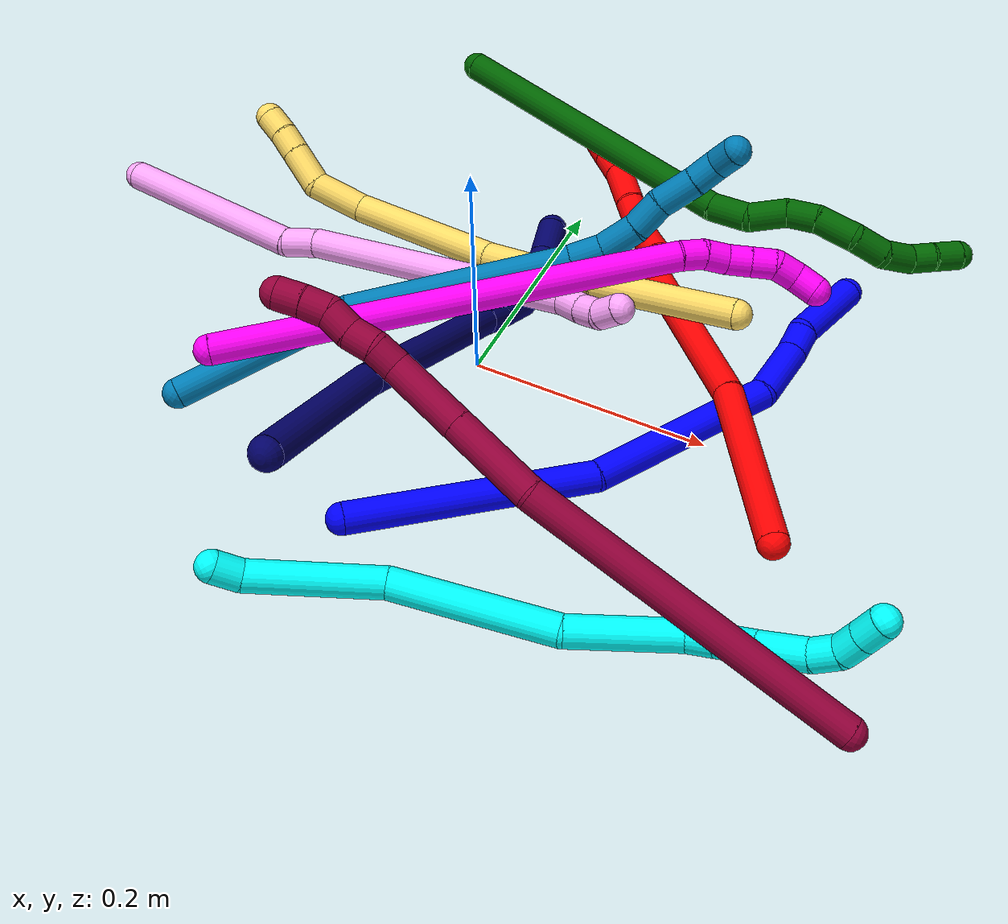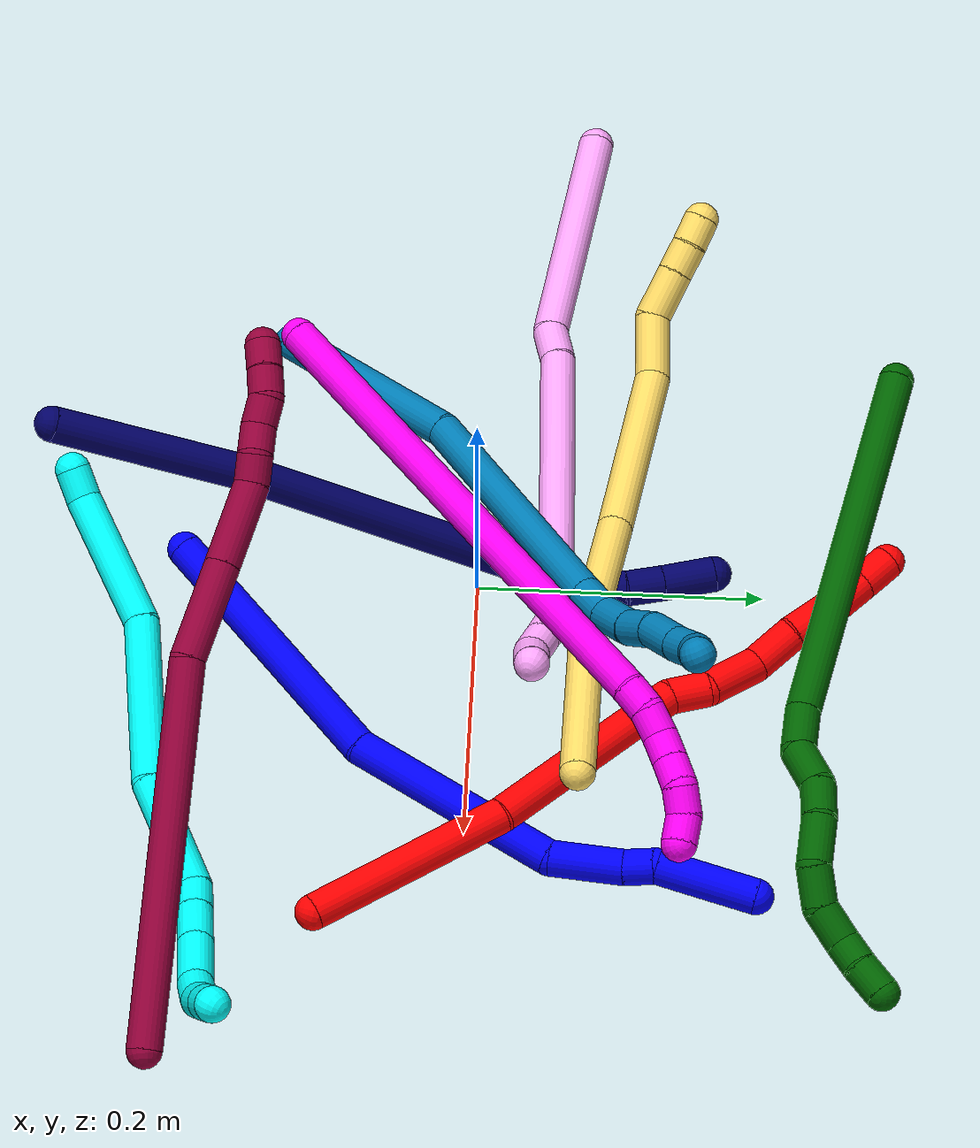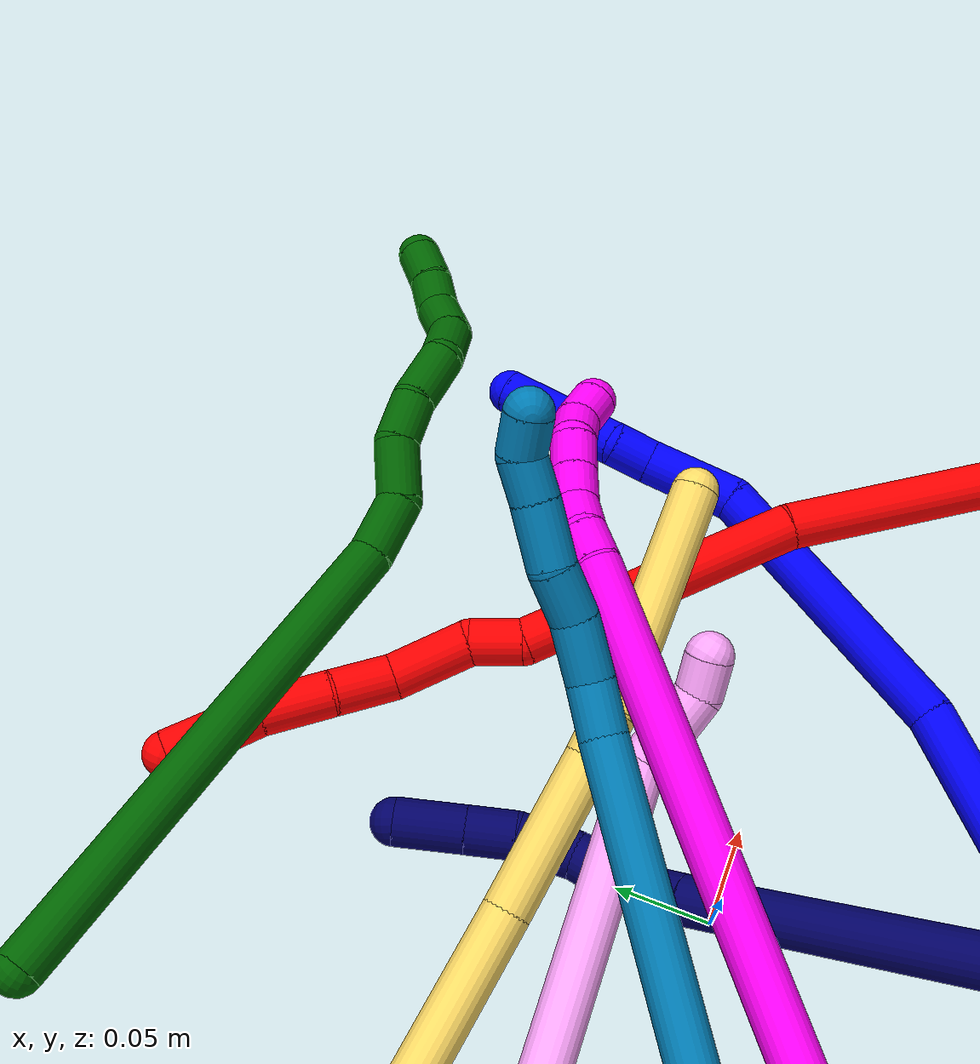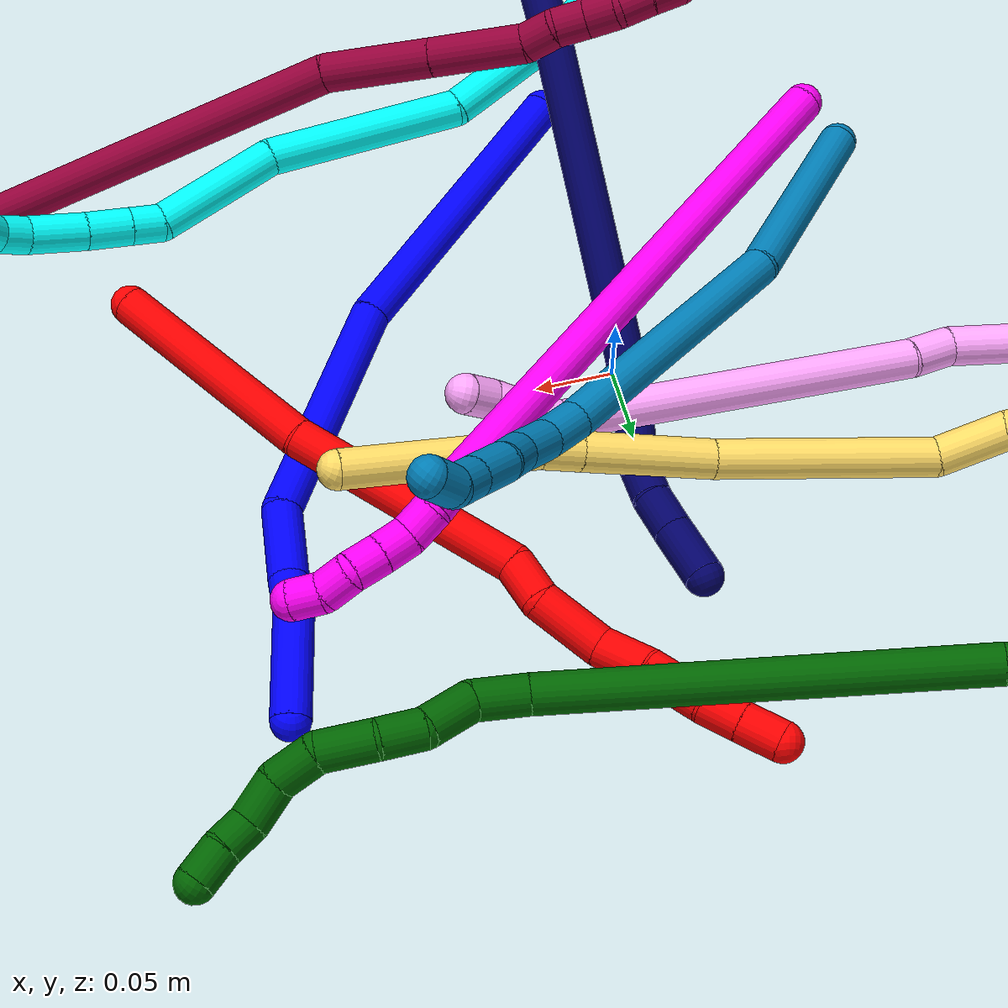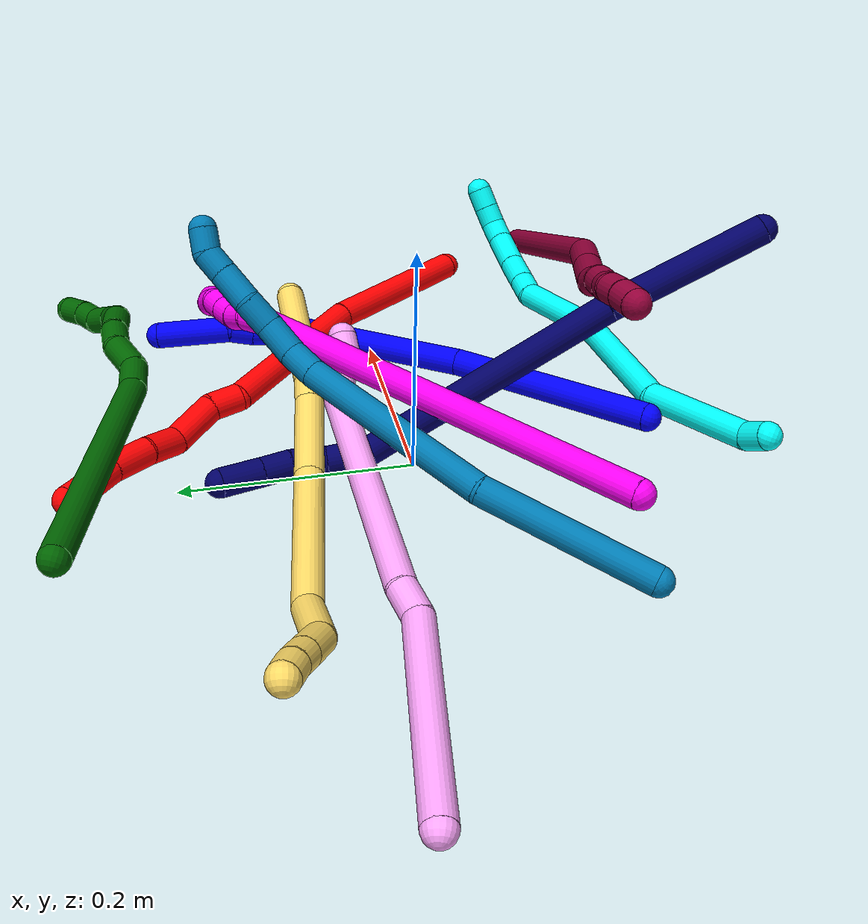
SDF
<sdf version="1.7">
 <world name="default">
  <plugin name="TubeGeneratorPlugin" filename="libtube_generator_plugin.so"/>
  <model name="photoneo_s_sensor">
   <static>1</static>
   <pose>0 0 2 1.57079 1.57079 3.14159</pose>
   <link name="link">
    <inertial><mass>0.1</mass></inertial>
    <sensor name="sensor" type="depth">
     <update_rate>30</update_rate>
     <camera>
      <horizontal_fov>1.22</horizontal_fov>
      <image><width>1920</width><height>1200</height><format>B8G8R8</format></image>
      <clip><near>0.1</near><far>2</far></clip>
      <depth_camera><output>points</output></depth_camera>
     </camera>
     <plugin name="camera_plugin" filename="libgazebo_ros_depth_camera.so">
      <baseline>0.2</baseline>
      <alwaysOn>1</alwaysOn>
      <updateRate>0.0</updateRate>
      <cameraName>camera_ir</cameraName>
      <imageTopicName>/camera/color/image_raw</imageTopicName>
      <cameraInfoTopicName>/camera/color/camera_info</cameraInfoTopicName>
      <depthImageTopicName>/camera/depth/image_raw</depthImageTopicName>
      <depthImageCameraInfoTopicName>/camera/depth/camera_info</depthImageCameraInfoTopicName>
      <pointCloudTopicName>/camera/depth/points</pointCloudTopicName>
      <frameName>fr_optical</frameName>
      <pointCloudCutoff>0.1</pointCloudCutoff>
      <pointCloudCutoffMax>2.0</pointCloudCutoffMax>
      <distortionK1>0</distortionK1>
      <distortionK2>0</distortionK2>
      <distortionK3>0</distortionK3>
      <distortionT1>0</distortionT1>
      <distortionT2>0</distortionT2>
      <CxPrime>0</CxPrime>
      <Cx>0</Cx>
      <Cy>0</Cy>
      <focalLength>0</focalLength>
      <hackBaseline>0</hackBaseline>
     </plugin>
    </sensor>
   </link>
  </model>
  <gravity>0 0 -9.8</gravity>
  <magnetic_field>6e-06 2.3e-05 -4.2e-05</magnetic_field>
  <atmosphere type="adiabatic"/>
  <physics name="default_physics" default="0" type="ode">
   <max_step_size>0.003</max_step_size>
   <real_time_factor>1</real_time_factor>
   <real_time_update_rate>1000</real_time_update_rate>
   <max_contacts>10000</max_contacts>
   <ode>
    <solver>
     <type>quick</type>
     <iters>100</iters>
     <sor>1.3</sor>
     <use_dynamic_moi_rescaling>0</use_dynamic_moi_rescaling>
    </solver>
    <constraints>
     <contact_max_correcting_vel>0</contact_max_correcting_vel>
     <contact_surface_layer>0.001</contact_surface_layer>
     <cfm>0</cfm>
     <erp>0.2</erp>
    </constraints>
   </ode>
  </physics>
  <scene><ambient>0.4 0.4 0.4 1</ambient><background>0.7 0.7 0.7 1</background><shadows>0</shadows></scene>
  <audio><device>default</device></audio>
  <spherical_coordinates>
   <surface_model>EARTH_WGS84</surface_model>
   <latitude_deg>0</latitude_deg>
   <longitude_deg>0</longitude_deg>
   <elevation>0</elevation>
   <heading_deg>0</heading_deg>
  </spherical_coordinates>
  <model name="bin">
   <static>1</static>
   <link name="bottom">
    <collision name="collision-bottom">
     <pose>0 0 -0.01 0 -0 0</pose>
     <geometry><box><size>0.8 0.6 0.02</size></box></geometry>
     <surface>
      <friction><ode><mu>100</mu><mu2>100</mu2></ode></friction>
      <contact><collide_bitmask>65535</collide_bitmask></contact>
     </surface>
    </collision>
   </link>
   <link name="west_wall">
    <collision name="collision-west_wall">
     <pose>-0.41 0 0.1 0 -0 0</pose>
     <geometry><box><size>0.02 0.6 0.2</size></box></geometry>
     <surface>
      <friction><ode><mu>100</mu><mu2>100</mu2></ode></friction>
      <contact><collide_bitmask>65535</collide_bitmask></contact>
     </surface>
    </collision>
   </link>
   <link name="east_wall">
    <collision name="collision-east_wall">
     <pose>0.41 0 0.1 0 -0 0</pose>
     <geometry><box><size>0.02 0.6 0.2</size></box></geometry>
     <surface>
      <friction><ode><mu>100</mu><mu2>100</mu2></ode></friction>
      <contact><collide_bitmask>65535</collide_bitmask></contact>
     </surface>
    </collision>
   </link>
   <link name="south_wall">
    <collision name="collision-south_wall">
     <pose>0 -0.31 0.1 0 -0 0</pose>
     <geometry><box><size>0.8 0.02 0.2</size></box></geometry>
     <surface>
      <friction><ode><mu>100</mu><mu2>100</mu2></ode></friction>
      <contact><collide_bitmask>65535</collide_bitmask></contact>
     </surface>
    </collision>
   </link>
   <link name="north_wall">
    <collision name="collision-north_wall">
     <pose>0 0.31 0.1 0 -0 0</pose>
     <geometry><box><size>0.8 0.02 0.2</size></box></geometry>
     <surface>
      <friction><ode><mu>100</mu><mu2>100</mu2></ode></friction>
      <contact><collide_bitmask>65535</collide_bitmask></contact>
     </surface>
    </collision>
   </link>
  </model>
  <model name="1">
   <static>0</static>
   <link name="1">
    <collision name="collision-cylinder-e_1_1_4">
     <pose>-0.056528 0.072189 -0.035755 -2.03067 -0.611869 0.941497</pose>
     <geometry><cylinder><radius>0.0125</radius><length>0.196825</length></cylinder></geometry>
     <surface>
      <friction><ode><mu>1.16</mu><mu2>1.16</mu2><slip1>0</slip1><slip2>0</slip2></ode></friction>
      <contact><ode><kp>1e+06</kp><kd>1</kd><max_vel>0</max_vel><min_depth>0.001</min_depth></ode></contact>
     </surface>
    </collision>
    <visual name="visual-cylinder-e_1_1_4">
     <pose>-0.056528 0.072189 -0.035755 -2.03067 -0.611869 0.941497</pose>
     <geometry><cylinder><radius>0.0125</radius><length>0.196825</length></cylinder></geometry>
     <material><ambient>0 0 1 1</ambient></material>
    </visual>
    <collision name="collision-cylinder-e_2_4_5">
     <pose>-0.175586 0.187292 -0.094243 -2.05796 -0.910455 1.36558</pose>
     <geometry><cylinder><radius>0.0125</radius><length>0.158346</length></cylinder></geometry>
     <surface>
      <friction><ode><mu>1.16</mu><mu2>1.16</mu2><slip1>0</slip1><slip2>0</slip2></ode></friction>
      <contact><ode><kp>1e+06</kp><kd>1</kd><max_vel>0</max_vel><min_depth>0.001</min_depth></ode></contact>
     </surface>
    </collision>
    <visual name="visual-cylinder-e_2_4_5">
     <pose>-0.175586 0.187292 -0.094243 -2.05796 -0.910455 1.36558</pose>
     <geometry><cylinder><radius>0.0125</radius><length>0.158346</length></cylinder></geometry>
     <material><ambient>0 0 1 1</ambient></material>
    </visual>
    <collision name="collision-cylinder-e_3_5_6">
     <pose>-0.262917 0.233619 -0.123517 -2.66053 -1.28167 2.50615</pose>
     <geometry><cylinder><radius>0.0125</radius><length>0.051752</length></cylinder></geometry>
     <surface>
      <friction><ode><mu>1.16</mu><mu2>1.16</mu2><slip1>0</slip1><slip2>0</slip2></ode></friction>
      <contact><ode><kp>1e+06</kp><kd>1</kd><max_vel>0</max_vel><min_depth>0.001</min_depth></ode></contact>
     </surface>
    </collision>
    <visual name="visual-cylinder-e_3_5_6">
     <pose>-0.262917 0.233619 -0.123517 -2.66053 -1.28167 2.50615</pose>
     <geometry><cylinder><radius>0.0125</radius><length>0.051752</length></cylinder></geometry>
     <material><ambient>0 0 1 1</ambient></material>
    </visual>
    <collision name="collision-cylinder-e_4_6_7">
     <pose>-0.298862 0.238176 -0.130409 -1.86924 -1.46391 1.76544</pose>
     <geometry><cylinder><radius>0.0125</radius><length>0.022414</length></cylinder></geometry>
     <surface>
      <friction><ode><mu>1.16</mu><mu2>1.16</mu2><slip1>0</slip1><slip2>0</slip2></ode></friction>
      <contact><ode><kp>1e+06</kp><kd>1</kd><max_vel>0</max_vel><min_depth>0.001</min_depth></ode></contact>
     </surface>
    </collision>
    <visual name="visual-cylinder-e_4_6_7">
     <pose>-0.298862 0.238176 -0.130409 -1.86924 -1.46391 1.76544</pose>
     <geometry><cylinder><radius>0.0125</radius><length>0.022414</length></cylinder></geometry>
     <material><ambient>0 0 1 1</ambient></material>
    </visual>
    <collision name="collision-cylinder-e_5_7_2">
     <pose>-0.341504 0.247161 -0.14471 -2.62943 -1.10072 2.33495</pose>
     <geometry><cylinder><radius>0.0125</radius><length>0.070663</length></cylinder></geometry>
     <surface>
      <friction><ode><mu>1.16</mu><mu2>1.16</mu2><slip1>0</slip1><slip2>0</slip2></ode></friction>
      <contact><ode><kp>1e+06</kp><kd>1</kd><max_vel>0</max_vel><min_depth>0.001</min_depth></ode></contact>
     </surface>
    </collision>
    <visual name="visual-cylinder-e_5_7_2">
     <pose>-0.341504 0.247161 -0.14471 -2.62943 -1.10072 2.33495</pose>
     <geometry><cylinder><radius>0.0125</radius><length>0.070663</length></cylinder></geometry>
     <material><ambient>0 0 1 1</ambient></material>
    </visual>
    <collision name="collision-sphere-2">
     <pose>-0.373003 0.255004 -0.158661 0 -0 0</pose>
     <geometry><sphere><radius>0.0125</radius></sphere></geometry>
     <surface>
      <friction><ode><mu>1.16</mu><mu2>1.16</mu2><slip1>0</slip1><slip2>0</slip2></ode></friction>
      <contact><ode><kp>1e+06</kp><kd>1</kd><max_vel>0</max_vel><min_depth>0.001</min_depth></ode></contact>
     </surface>
    </collision>
    <visual name="visual-sphere-2">
     <pose>-0.373003 0.255004 -0.158661 0 -0 0</pose>
     <geometry><sphere><radius>0.0125</radius></sphere></geometry>
     <material><ambient>0 0 1 1</ambient></material>
    </visual>
    <collision name="collision-sphere-7">
     <pose>-0.310005 0.239319 -0.13076 0 -0 0</pose>
     <geometry><sphere><radius>0.0125</radius></sphere></geometry>
     <surface>
      <friction><ode><mu>1.16</mu><mu2>1.16</mu2><slip1>0</slip1><slip2>0</slip2></ode></friction>
      <contact><ode><kp>1e+06</kp><kd>1</kd><max_vel>0</max_vel><min_depth>0.001</min_depth></ode></contact>
     </surface>
    </collision>
    <visual name="visual-sphere-7">
     <pose>-0.310005 0.239319 -0.13076 0 -0 0</pose>
     <geometry><sphere><radius>0.0125</radius></sphere></geometry>
     <material><ambient>0 0 1 1</ambient></material>
    </visual>
    <collision name="collision-sphere-6">
     <pose>-0.287719 0.237033 -0.130057 0 -0 0</pose>
     <geometry><sphere><radius>0.0125</radius></sphere></geometry>
     <surface>
      <friction><ode><mu>1.16</mu><mu2>1.16</mu2><slip1>0</slip1><slip2>0</slip2></ode></friction>
      <contact><ode><kp>1e+06</kp><kd>1</kd><max_vel>0</max_vel><min_depth>0.001</min_depth></ode></contact>
     </surface>
    </collision>
    <visual name="visual-sphere-6">
     <pose>-0.287719 0.237033 -0.130057 0 -0 0</pose>
     <geometry><sphere><radius>0.0125</radius></sphere></geometry>
     <material><ambient>0 0 1 1</ambient></material>
    </visual>
    <collision name="collision-sphere-5">
     <pose>-0.238115 0.230206 -0.116977 0 -0 0</pose>
     <geometry><sphere><radius>0.0125</radius></sphere></geometry>
     <surface>
      <friction><ode><mu>1.16</mu><mu2>1.16</mu2><slip1>0</slip1><slip2>0</slip2></ode></friction>
      <contact><ode><kp>1e+06</kp><kd>1</kd><max_vel>0</max_vel><min_depth>0.001</min_depth></ode></contact>
     </surface>
    </collision>
    <visual name="visual-sphere-5">
     <pose>-0.238115 0.230206 -0.116977 0 -0 0</pose>
     <geometry><sphere><radius>0.0125</radius></sphere></geometry>
     <material><ambient>0 0 1 1</ambient></material>
    </visual>
    <collision name="collision-sphere-1">
     <geometry><sphere><radius>0.0125</radius></sphere></geometry>
     <surface>
      <friction><ode><mu>1.16</mu><mu2>1.16</mu2><slip1>0</slip1><slip2>0</slip2></ode></friction>
      <contact><ode><kp>1e+06</kp><kd>1</kd><max_vel>0</max_vel><min_depth>0.001</min_depth></ode></contact>
     </surface>
    </collision>
    <visual name="visual-sphere-1">
     <geometry><sphere><radius>0.0125</radius></sphere></geometry>
     <material><ambient>0 0 1 1</ambient></material>
    </visual>
    <collision name="collision-sphere-4">
     <pose>-0.113056 0.144378 -0.071509 0 -0 0</pose>
     <geometry><sphere><radius>0.0125</radius></sphere></geometry>
     <surface>
      <friction><ode><mu>1.16</mu><mu2>1.16</mu2><slip1>0</slip1><slip2>0</slip2></ode></friction>
      <contact><ode><kp>1e+06</kp><kd>1</kd><max_vel>0</max_vel><min_depth>0.001</min_depth></ode></contact>
     </surface>
    </collision>
    <visual name="visual-sphere-4">
     <pose>-0.113056 0.144378 -0.071509 0 -0 0</pose>
     <geometry><sphere><radius>0.0125</radius></sphere></geometry>
     <material><ambient>0 0 1 1</ambient></material>
    </visual>
    <inertial>
     <pose>-0.166733 0.157519 -0.083003 0 -0 0</pose>
     <mass>0.5</mass>
     <inertia><ixx>0.000951</ixx><ixy>0</ixy><ixz>0</ixz><iyy>0.001003</iyy><iyz>0</iyz><izz>3e-06</izz></inertia>
    </inertial>
   </link>
   <pose>-0.005302 -0.204925 0.026626 0.179667 0.250818 -1.5045</pose>
  </model>
  <model name="2">
   <static>0</static>
   <link name="2">
    <collision name="collision-cylinder-e_1_1_4">
     <pose>-0.033554 0.03846 0.053994 -0.618941 -0.46857 0.15233</pose>
     <geometry><cylinder><radius>0.0125</radius><length>0.148599</length></cylinder></geometry>
     <surface>
      <friction><ode><mu>1.16</mu><mu2>1.16</mu2><slip1>0</slip1><slip2>0</slip2></ode></friction>
      <contact><ode><kp>1e+06</kp><kd>1</kd><max_vel>0</max_vel><min_depth>0.001</min_depth></ode></contact>
     </surface>
    </collision>
    <visual name="visual-cylinder-e_1_1_4">
     <pose>-0.033554 0.03846 0.053994 -0.618941 -0.46857 0.15233</pose>
     <geometry><cylinder><radius>0.0125</radius><length>0.148599</length></cylinder></geometry>
     <material><ambient>1 0 0 1</ambient></material>
    </visual>
    <collision name="collision-cylinder-e_2_4_5">
     <pose>-0.099457 0.129042 0.155318 -0.833537 -0.4307 0.193073</pose>
     <geometry><cylinder><radius>0.0125</radius><length>0.154961</length></cylinder></geometry>
     <surface>
      <friction><ode><mu>1.16</mu><mu2>1.16</mu2><slip1>0</slip1><slip2>0</slip2></ode></friction>
      <contact><ode><kp>1e+06</kp><kd>1</kd><max_vel>0</max_vel><min_depth>0.001</min_depth></ode></contact>
     </surface>
    </collision>
    <visual name="visual-cylinder-e_2_4_5">
     <pose>-0.099457 0.129042 0.155318 -0.833537 -0.4307 0.193073</pose>
     <geometry><cylinder><radius>0.0125</radius><length>0.154961</length></cylinder></geometry>
     <material><ambient>1 0 0 1</ambient></material>
    </visual>
    <collision name="collision-cylinder-e_3_5_6">
     <pose>-0.136293 0.185952 0.215072 -0.367914 -0.325043 0.060997</pose>
     <geometry><cylinder><radius>0.0125</radius><length>0.028102</length></cylinder></geometry>
     <surface>
      <friction><ode><mu>1.16</mu><mu2>1.16</mu2><slip1>0</slip1><slip2>0</slip2></ode></friction>
      <contact><ode><kp>1e+06</kp><kd>1</kd><max_vel>0</max_vel><min_depth>0.001</min_depth></ode></contact>
     </surface>
    </collision>
    <visual name="visual-cylinder-e_3_5_6">
     <pose>-0.136293 0.185952 0.215072 -0.367914 -0.325043 0.060997</pose>
     <geometry><cylinder><radius>0.0125</radius><length>0.028102</length></cylinder></geometry>
     <material><ambient>1 0 0 1</ambient></material>
    </visual>
    <collision name="collision-cylinder-e_4_6_7">
     <pose>-0.14634 0.206564 0.242648 -0.807063 -0.248538 0.106565</pose>
     <geometry><cylinder><radius>0.0125</radius><length>0.045203</length></cylinder></geometry>
     <surface>
      <friction><ode><mu>1.16</mu><mu2>1.16</mu2><slip1>0</slip1><slip2>0</slip2></ode></friction>
      <contact><ode><kp>1e+06</kp><kd>1</kd><max_vel>0</max_vel><min_depth>0.001</min_depth></ode></contact>
     </surface>
    </collision>
    <visual name="visual-cylinder-e_4_6_7">
     <pose>-0.14634 0.206564 0.242648 -0.807063 -0.248538 0.106565</pose>
     <geometry><cylinder><radius>0.0125</radius><length>0.045203</length></cylinder></geometry>
     <material><ambient>1 0 0 1</ambient></material>
    </visual>
    <collision name="collision-cylinder-e_5_7_8">
     <pose>-0.163159 0.23093 0.267495 -0.7223 -0.716738 0.281076</pose>
     <geometry><cylinder><radius>0.0125</radius><length>0.034279</length></cylinder></geometry>
     <surface>
      <friction><ode><mu>1.16</mu><mu2>1.16</mu2><slip1>0</slip1><slip2>0</slip2></ode></friction>
      <contact><ode><kp>1e+06</kp><kd>1</kd><max_vel>0</max_vel><min_depth>0.001</min_depth></ode></contact>
     </surface>
    </collision>
    <visual name="visual-cylinder-e_5_7_8">
     <pose>-0.163159 0.23093 0.267495 -0.7223 -0.716738 0.281076</pose>
     <geometry><cylinder><radius>0.0125</radius><length>0.034279</length></cylinder></geometry>
     <material><ambient>1 0 0 1</ambient></material>
    </visual>
    <collision name="collision-cylinder-e_6_8_9">
     <pose>-0.184611 0.249858 0.289684 -0.693451 -0.560295 0.207171</pose>
     <geometry><cylinder><radius>0.0125</radius><length>0.038356</length></cylinder></geometry>
     <surface>
      <friction><ode><mu>1.16</mu><mu2>1.16</mu2><slip1>0</slip1><slip2>0</slip2></ode></friction>
      <contact><ode><kp>1e+06</kp><kd>1</kd><max_vel>0</max_vel><min_depth>0.001</min_depth></ode></contact>
     </surface>
    </collision>
    <visual name="visual-cylinder-e_6_8_9">
     <pose>-0.184611 0.249858 0.289684 -0.693451 -0.560295 0.207171</pose>
     <geometry><cylinder><radius>0.0125</radius><length>0.038356</length></cylinder></geometry>
     <material><ambient>1 0 0 1</ambient></material>
    </visual>
    <collision name="collision-cylinder-e_7_9_10">
     <pose>-0.20051 0.268487 0.309075 -0.874193 -0.488063 0.231638</pose>
     <geometry><cylinder><radius>0.0125</radius><length>0.024342</length></cylinder></geometry>
     <surface>
      <friction><ode><mu>1.16</mu><mu2>1.16</mu2><slip1>0</slip1><slip2>0</slip2></ode></friction>
      <contact><ode><kp>1e+06</kp><kd>1</kd><max_vel>0</max_vel><min_depth>0.001</min_depth></ode></contact>
     </surface>
    </collision>
    <visual name="visual-cylinder-e_7_9_10">
     <pose>-0.20051 0.268487 0.309075 -0.874193 -0.488063 0.231638</pose>
     <geometry><cylinder><radius>0.0125</radius><length>0.024342</length></cylinder></geometry>
     <material><ambient>1 0 0 1</ambient></material>
    </visual>
    <collision name="collision-cylinder-e_8_10_2">
     <pose>-0.212886 0.285257 0.323315 -0.859795 -0.535092 0.250053</pose>
     <geometry><cylinder><radius>0.0125</radius><length>0.026157</length></cylinder></geometry>
     <surface>
      <friction><ode><mu>1.16</mu><mu2>1.16</mu2><slip1>0</slip1><slip2>0</slip2></ode></friction>
      <contact><ode><kp>1e+06</kp><kd>1</kd><max_vel>0</max_vel><min_depth>0.001</min_depth></ode></contact>
     </surface>
    </collision>
    <visual name="visual-cylinder-e_8_10_2">
     <pose>-0.212886 0.285257 0.323315 -0.859795 -0.535092 0.250053</pose>
     <geometry><cylinder><radius>0.0125</radius><length>0.026157</length></cylinder></geometry>
     <material><ambient>1 0 0 1</ambient></material>
    </visual>
    <collision name="collision-sphere-2">
     <pose>-0.219555 0.293782 0.330656 0 -0 0</pose>
     <geometry><sphere><radius>0.0125</radius></sphere></geometry>
     <surface>
      <friction><ode><mu>1.16</mu><mu2>1.16</mu2><slip1>0</slip1><slip2>0</slip2></ode></friction>
      <contact><ode><kp>1e+06</kp><kd>1</kd><max_vel>0</max_vel><min_depth>0.001</min_depth></ode></contact>
     </surface>
    </collision>
    <visual name="visual-sphere-2">
     <pose>-0.219555 0.293782 0.330656 0 -0 0</pose>
     <geometry><sphere><radius>0.0125</radius></sphere></geometry>
     <material><ambient>1 0 0 1</ambient></material>
    </visual>
    <collision name="collision-sphere-10">
     <pose>-0.206217 0.276733 0.315973 0 -0 0</pose>
     <geometry><sphere><radius>0.0125</radius></sphere></geometry>
     <surface>
      <friction><ode><mu>1.16</mu><mu2>1.16</mu2><slip1>0</slip1><slip2>0</slip2></ode></friction>
      <contact><ode><kp>1e+06</kp><kd>1</kd><max_vel>0</max_vel><min_depth>0.001</min_depth></ode></contact>
     </surface>
    </collision>
    <visual name="visual-sphere-10">
     <pose>-0.206217 0.276733 0.315973 0 -0 0</pose>
     <geometry><sphere><radius>0.0125</radius></sphere></geometry>
     <material><ambient>1 0 0 1</ambient></material>
    </visual>
    <collision name="collision-sphere-9">
     <pose>-0.194803 0.260242 0.302178 0 -0 0</pose>
     <geometry><sphere><radius>0.0125</radius></sphere></geometry>
     <surface>
      <friction><ode><mu>1.16</mu><mu2>1.16</mu2><slip1>0</slip1><slip2>0</slip2></ode></friction>
      <contact><ode><kp>1e+06</kp><kd>1</kd><max_vel>0</max_vel><min_depth>0.001</min_depth></ode></contact>
     </surface>
    </collision>
    <visual name="visual-sphere-9">
     <pose>-0.194803 0.260242 0.302178 0 -0 0</pose>
     <geometry><sphere><radius>0.0125</radius></sphere></geometry>
     <material><ambient>1 0 0 1</ambient></material>
    </visual>
    <collision name="collision-sphere-4">
     <pose>-0.067109 0.076921 0.107987 0 -0 0</pose>
     <geometry><sphere><radius>0.0125</radius></sphere></geometry>
     <surface>
      <friction><ode><mu>1.16</mu><mu2>1.16</mu2><slip1>0</slip1><slip2>0</slip2></ode></friction>
      <contact><ode><kp>1e+06</kp><kd>1</kd><max_vel>0</max_vel><min_depth>0.001</min_depth></ode></contact>
     </surface>
    </collision>
    <visual name="visual-sphere-4">
     <pose>-0.067109 0.076921 0.107987 0 -0 0</pose>
     <geometry><sphere><radius>0.0125</radius></sphere></geometry>
     <material><ambient>1 0 0 1</ambient></material>
    </visual>
    <collision name="collision-sphere-1">
     <geometry><sphere><radius>0.0125</radius></sphere></geometry>
     <surface>
      <friction><ode><mu>1.16</mu><mu2>1.16</mu2><slip1>0</slip1><slip2>0</slip2></ode></friction>
      <contact><ode><kp>1e+06</kp><kd>1</kd><max_vel>0</max_vel><min_depth>0.001</min_depth></ode></contact>
     </surface>
    </collision>
    <visual name="visual-sphere-1">
     <geometry><sphere><radius>0.0125</radius></sphere></geometry>
     <material><ambient>1 0 0 1</ambient></material>
    </visual>
    <collision name="collision-sphere-8">
     <pose>-0.174419 0.239473 0.27719 0 -0 0</pose>
     <geometry><sphere><radius>0.0125</radius></sphere></geometry>
     <surface>
      <friction><ode><mu>1.16</mu><mu2>1.16</mu2><slip1>0</slip1><slip2>0</slip2></ode></friction>
      <contact><ode><kp>1e+06</kp><kd>1</kd><max_vel>0</max_vel><min_depth>0.001</min_depth></ode></contact>
     </surface>
    </collision>
    <visual name="visual-sphere-8">
     <pose>-0.174419 0.239473 0.27719 0 -0 0</pose>
     <geometry><sphere><radius>0.0125</radius></sphere></geometry>
     <material><ambient>1 0 0 1</ambient></material>
    </visual>
    <collision name="collision-sphere-5">
     <pose>-0.131806 0.181163 0.202648 0 -0 0</pose>
     <geometry><sphere><radius>0.0125</radius></sphere></geometry>
     <surface>
      <friction><ode><mu>1.16</mu><mu2>1.16</mu2><slip1>0</slip1><slip2>0</slip2></ode></friction>
      <contact><ode><kp>1e+06</kp><kd>1</kd><max_vel>0</max_vel><min_depth>0.001</min_depth></ode></contact>
     </surface>
    </collision>
    <visual name="visual-sphere-5">
     <pose>-0.131806 0.181163 0.202648 0 -0 0</pose>
     <geometry><sphere><radius>0.0125</radius></sphere></geometry>
     <material><ambient>1 0 0 1</ambient></material>
    </visual>
    <collision name="collision-sphere-6">
     <pose>-0.14078 0.190742 0.227496 0 -0 0</pose>
     <geometry><sphere><radius>0.0125</radius></sphere></geometry>
     <surface>
      <friction><ode><mu>1.16</mu><mu2>1.16</mu2><slip1>0</slip1><slip2>0</slip2></ode></friction>
      <contact><ode><kp>1e+06</kp><kd>1</kd><max_vel>0</max_vel><min_depth>0.001</min_depth></ode></contact>
     </surface>
    </collision>
    <visual name="visual-sphere-6">
     <pose>-0.14078 0.190742 0.227496 0 -0 0</pose>
     <geometry><sphere><radius>0.0125</radius></sphere></geometry>
     <material><ambient>1 0 0 1</ambient></material>
    </visual>
    <collision name="collision-sphere-7">
     <pose>-0.1519 0.222387 0.257799 0 -0 0</pose>
     <geometry><sphere><radius>0.0125</radius></sphere></geometry>
     <surface>
      <friction><ode><mu>1.16</mu><mu2>1.16</mu2><slip1>0</slip1><slip2>0</slip2></ode></friction>
      <contact><ode><kp>1e+06</kp><kd>1</kd><max_vel>0</max_vel><min_depth>0.001</min_depth></ode></contact>
     </surface>
    </collision>
    <visual name="visual-sphere-7">
     <pose>-0.1519 0.222387 0.257799 0 -0 0</pose>
     <geometry><sphere><radius>0.0125</radius></sphere></geometry>
     <material><ambient>1 0 0 1</ambient></material>
    </visual>
    <inertial>
     <pose>-0.107933 0.143543 0.170731 0 -0 0</pose>
     <mass>0.5</mass>
     <inertia>
      <ixx>0.000633</ixx>
      <ixy>0</ixy>
      <ixz>0</ixz>
      <iyy>0.000605</iyy>
      <iyz>0</iyz>
      <izz>-7.8e-05</izz>
     </inertia>
    </inertial>
   </link>
   <pose>0.289587 -0.096994 0.038707 -2.01373 1.03836 -0.529512</pose>
  </model>
  <model name="3">
   <static>0</static>
   <link name="3">
    <collision name="collision-cylinder-e_1_1_4">
     <pose>0.007555 -0.003496 -0.007807 2.72053 0.723436 2.11333</pose>
     <geometry><cylinder><radius>0.0125</radius><length>0.022826</length></cylinder></geometry>
     <surface>
      <friction><ode><mu>1.16</mu><mu2>1.16</mu2><slip1>0</slip1><slip2>0</slip2></ode></friction>
      <contact><ode><kp>1e+06</kp><kd>1</kd><max_vel>0</max_vel><min_depth>0.001</min_depth></ode></contact>
     </surface>
    </collision>
    <visual name="visual-cylinder-e_1_1_4">
     <pose>0.007555 -0.003496 -0.007807 2.72053 0.723436 2.11333</pose>
     <geometry><cylinder><radius>0.0125</radius><length>0.022826</length></cylinder></geometry>
     <material><ambient>0.003922 1 0.996078 1</ambient></material>
    </visual>
    <collision name="collision-cylinder-e_2_4_5">
     <pose>0.042036 -0.006249 -0.060483 -3.12501 0.540441 -3.08174</pose>
     <geometry><cylinder><radius>0.0125</radius><length>0.104666</length></cylinder></geometry>
     <surface>
      <friction><ode><mu>1.16</mu><mu2>1.16</mu2><slip1>0</slip1><slip2>0</slip2></ode></friction>
      <contact><ode><kp>1e+06</kp><kd>1</kd><max_vel>0</max_vel><min_depth>0.001</min_depth></ode></contact>
     </surface>
    </collision>
    <visual name="visual-cylinder-e_2_4_5">
     <pose>0.042036 -0.006249 -0.060483 -3.12501 0.540441 -3.08174</pose>
     <geometry><cylinder><radius>0.0125</radius><length>0.104666</length></cylinder></geometry>
     <material><ambient>0.003922 1 0.996078 1</ambient></material>
    </visual>
    <collision name="collision-cylinder-e_3_5_6">
     <pose>0.11342 0.014511 -0.150178 -2.72165 0.735901 -2.13159</pose>
     <geometry><cylinder><radius>0.0125</radius><length>0.132462</length></cylinder></geometry>
     <surface>
      <friction><ode><mu>1.16</mu><mu2>1.16</mu2><slip1>0</slip1><slip2>0</slip2></ode></friction>
      <contact><ode><kp>1e+06</kp><kd>1</kd><max_vel>0</max_vel><min_depth>0.001</min_depth></ode></contact>
     </surface>
    </collision>
    <visual name="visual-cylinder-e_3_5_6">
     <pose>0.11342 0.014511 -0.150178 -2.72165 0.735901 -2.13159</pose>
     <geometry><cylinder><radius>0.0125</radius><length>0.132462</length></cylinder></geometry>
     <material><ambient>0.003922 1 0.996078 1</ambient></material>
    </visual>
    <collision name="collision-cylinder-e_4_6_7">
     <pose>0.17999 0.038911 -0.232491 -3.02514 0.529969 -2.7184</pose>
     <geometry><cylinder><radius>0.0125</radius><length>0.087487</length></cylinder></geometry>
     <surface>
      <friction><ode><mu>1.16</mu><mu2>1.16</mu2><slip1>0</slip1><slip2>0</slip2></ode></friction>
      <contact><ode><kp>1e+06</kp><kd>1</kd><max_vel>0</max_vel><min_depth>0.001</min_depth></ode></contact>
     </surface>
    </collision>
    <visual name="visual-cylinder-e_4_6_7">
     <pose>0.17999 0.038911 -0.232491 -3.02514 0.529969 -2.7184</pose>
     <geometry><cylinder><radius>0.0125</radius><length>0.087487</length></cylinder></geometry>
     <material><ambient>0.003922 1 0.996078 1</ambient></material>
    </visual>
    <collision name="collision-cylinder-e_5_7_8">
     <pose>0.208222 0.048408 -0.277355 -2.53555 0.598497 -1.55747</pose>
     <geometry><cylinder><radius>0.0125</radius><length>0.021724</length></cylinder></geometry>
     <surface>
      <friction><ode><mu>1.16</mu><mu2>1.16</mu2><slip1>0</slip1><slip2>0</slip2></ode></friction>
      <contact><ode><kp>1e+06</kp><kd>1</kd><max_vel>0</max_vel><min_depth>0.001</min_depth></ode></contact>
     </surface>
    </collision>
    <visual name="visual-cylinder-e_5_7_8">
     <pose>0.208222 0.048408 -0.277355 -2.53555 0.598497 -1.55747</pose>
     <geometry><cylinder><radius>0.0125</radius><length>0.021724</length></cylinder></geometry>
     <material><ambient>0.003922 1 0.996078 1</ambient></material>
    </visual>
    <collision name="collision-cylinder-e_6_8_9">
     <pose>0.222727 0.060524 -0.294814 -2.5345 0.599154 -1.55681</pose>
     <geometry><cylinder><radius>0.0125</radius><length>0.029735</length></cylinder></geometry>
     <surface>
      <friction><ode><mu>1.16</mu><mu2>1.16</mu2><slip1>0</slip1><slip2>0</slip2></ode></friction>
      <contact><ode><kp>1e+06</kp><kd>1</kd><max_vel>0</max_vel><min_depth>0.001</min_depth></ode></contact>
     </surface>
    </collision>
    <visual name="visual-cylinder-e_6_8_9">
     <pose>0.222727 0.060524 -0.294814 -2.5345 0.599154 -1.55681</pose>
     <geometry><cylinder><radius>0.0125</radius><length>0.029735</length></cylinder></geometry>
     <material><ambient>0.003922 1 0.996078 1</ambient></material>
    </visual>
    <collision name="collision-cylinder-e_7_9_10">
     <pose>0.24145 0.077616 -0.317971 -2.48438 0.559404 -1.40013</pose>
     <geometry><cylinder><radius>0.0125</radius><length>0.038965</length></cylinder></geometry>
     <surface>
      <friction><ode><mu>1.16</mu><mu2>1.16</mu2><slip1>0</slip1><slip2>0</slip2></ode></friction>
      <contact><ode><kp>1e+06</kp><kd>1</kd><max_vel>0</max_vel><min_depth>0.001</min_depth></ode></contact>
     </surface>
    </collision>
    <visual name="visual-cylinder-e_7_9_10">
     <pose>0.24145 0.077616 -0.317971 -2.48438 0.559404 -1.40013</pose>
     <geometry><cylinder><radius>0.0125</radius><length>0.038965</length></cylinder></geometry>
     <material><ambient>0.003922 1 0.996078 1</ambient></material>
    </visual>
    <collision name="collision-cylinder-e_8_10_11">
     <pose>0.254821 0.094619 -0.338993 -2.42562 0.280216 -0.721018</pose>
     <geometry><cylinder><radius>0.0125</radius><length>0.021928</length></cylinder></geometry>
     <surface>
      <friction><ode><mu>1.16</mu><mu2>1.16</mu2><slip1>0</slip1><slip2>0</slip2></ode></friction>
      <contact><ode><kp>1e+06</kp><kd>1</kd><max_vel>0</max_vel><min_depth>0.001</min_depth></ode></contact>
     </surface>
    </collision>
    <visual name="visual-cylinder-e_8_10_11">
     <pose>0.254821 0.094619 -0.338993 -2.42562 0.280216 -0.721018</pose>
     <geometry><cylinder><radius>0.0125</radius><length>0.021928</length></cylinder></geometry>
     <material><ambient>0.003922 1 0.996078 1</ambient></material>
    </visual>
    <collision name="collision-cylinder-e_9_11_12">
     <pose>0.256343 0.108744 -0.353727 -2.32585 -0.151325 0.347343</pose>
     <geometry><cylinder><radius>0.0125</radius><length>0.020028</length></cylinder></geometry>
     <surface>
      <friction><ode><mu>1.16</mu><mu2>1.16</mu2><slip1>0</slip1><slip2>0</slip2></ode></friction>
      <contact><ode><kp>1e+06</kp><kd>1</kd><max_vel>0</max_vel><min_depth>0.001</min_depth></ode></contact>
     </surface>
    </collision>
    <visual name="visual-cylinder-e_9_11_12">
     <pose>0.256343 0.108744 -0.353727 -2.32585 -0.151325 0.347343</pose>
     <geometry><cylinder><radius>0.0125</radius><length>0.020028</length></cylinder></geometry>
     <material><ambient>0.003922 1 0.996078 1</ambient></material>
    </visual>
    <collision name="collision-cylinder-e_10_12_2">
     <pose>0.253173 0.123317 -0.367207 -2.30873 -0.165329 0.370357</pose>
     <geometry><cylinder><radius>0.0125</radius><length>0.02018</length></cylinder></geometry>
     <surface>
      <friction><ode><mu>1.16</mu><mu2>1.16</mu2><slip1>0</slip1><slip2>0</slip2></ode></friction>
      <contact><ode><kp>1e+06</kp><kd>1</kd><max_vel>0</max_vel><min_depth>0.001</min_depth></ode></contact>
     </surface>
    </collision>
    <visual name="visual-cylinder-e_10_12_2">
     <pose>0.253173 0.123317 -0.367207 -2.30873 -0.165329 0.370357</pose>
     <geometry><cylinder><radius>0.0125</radius><length>0.02018</length></cylinder></geometry>
     <material><ambient>0.003922 1 0.996078 1</ambient></material>
    </visual>
    <collision name="collision-sphere-2">
     <pose>0.251513 0.13068 -0.373903 0 -0 0</pose>
     <geometry><sphere><radius>0.0125</radius></sphere></geometry>
     <surface>
      <friction><ode><mu>1.16</mu><mu2>1.16</mu2><slip1>0</slip1><slip2>0</slip2></ode></friction>
      <contact><ode><kp>1e+06</kp><kd>1</kd><max_vel>0</max_vel><min_depth>0.001</min_depth></ode></contact>
     </surface>
    </collision>
    <visual name="visual-sphere-2">
     <pose>0.251513 0.13068 -0.373903 0 -0 0</pose>
     <geometry><sphere><radius>0.0125</radius></sphere></geometry>
     <material><ambient>0.003922 1 0.996078 1</ambient></material>
    </visual>
    <collision name="collision-sphere-12">
     <pose>0.254834 0.115953 -0.360511 0 -0 0</pose>
     <geometry><sphere><radius>0.0125</radius></sphere></geometry>
     <surface>
      <friction><ode><mu>1.16</mu><mu2>1.16</mu2><slip1>0</slip1><slip2>0</slip2></ode></friction>
      <contact><ode><kp>1e+06</kp><kd>1</kd><max_vel>0</max_vel><min_depth>0.001</min_depth></ode></contact>
     </surface>
    </collision>
    <visual name="visual-sphere-12">
     <pose>0.254834 0.115953 -0.360511 0 -0 0</pose>
     <geometry><sphere><radius>0.0125</radius></sphere></geometry>
     <material><ambient>0.003922 1 0.996078 1</ambient></material>
    </visual>
    <collision name="collision-sphere-11">
     <pose>0.257853 0.101535 -0.346942 0 -0 0</pose>
     <geometry><sphere><radius>0.0125</radius></sphere></geometry>
     <surface>
      <friction><ode><mu>1.16</mu><mu2>1.16</mu2><slip1>0</slip1><slip2>0</slip2></ode></friction>
      <contact><ode><kp>1e+06</kp><kd>1</kd><max_vel>0</max_vel><min_depth>0.001</min_depth></ode></contact>
     </surface>
    </collision>
    <visual name="visual-sphere-11">
     <pose>0.257853 0.101535 -0.346942 0 -0 0</pose>
     <geometry><sphere><radius>0.0125</radius></sphere></geometry>
     <material><ambient>0.003922 1 0.996078 1</ambient></material>
    </visual>
    <collision name="collision-sphere-10">
     <pose>0.251789 0.087704 -0.331044 0 -0 0</pose>
     <geometry><sphere><radius>0.0125</radius></sphere></geometry>
     <surface>
      <friction><ode><mu>1.16</mu><mu2>1.16</mu2><slip1>0</slip1><slip2>0</slip2></ode></friction>
      <contact><ode><kp>1e+06</kp><kd>1</kd><max_vel>0</max_vel><min_depth>0.001</min_depth></ode></contact>
     </surface>
    </collision>
    <visual name="visual-sphere-10">
     <pose>0.251789 0.087704 -0.331044 0 -0 0</pose>
     <geometry><sphere><radius>0.0125</radius></sphere></geometry>
     <material><ambient>0.003922 1 0.996078 1</ambient></material>
    </visual>
    <collision name="collision-sphere-9">
     <pose>0.231111 0.067528 -0.304898 0 -0 0</pose>
     <geometry><sphere><radius>0.0125</radius></sphere></geometry>
     <surface>
      <friction><ode><mu>1.16</mu><mu2>1.16</mu2><slip1>0</slip1><slip2>0</slip2></ode></friction>
      <contact><ode><kp>1e+06</kp><kd>1</kd><max_vel>0</max_vel><min_depth>0.001</min_depth></ode></contact>
     </surface>
    </collision>
    <visual name="visual-sphere-9">
     <pose>0.231111 0.067528 -0.304898 0 -0 0</pose>
     <geometry><sphere><radius>0.0125</radius></sphere></geometry>
     <material><ambient>0.003922 1 0.996078 1</ambient></material>
    </visual>
    <collision name="collision-sphere-4">
     <pose>0.01511 -0.006993 -0.015614 0 -0 0</pose>
     <geometry><sphere><radius>0.0125</radius></sphere></geometry>
     <surface>
      <friction><ode><mu>1.16</mu><mu2>1.16</mu2><slip1>0</slip1><slip2>0</slip2></ode></friction>
      <contact><ode><kp>1e+06</kp><kd>1</kd><max_vel>0</max_vel><min_depth>0.001</min_depth></ode></contact>
     </surface>
    </collision>
    <visual name="visual-sphere-4">
     <pose>0.01511 -0.006993 -0.015614 0 -0 0</pose>
     <geometry><sphere><radius>0.0125</radius></sphere></geometry>
     <material><ambient>0.003922 1 0.996078 1</ambient></material>
    </visual>
    <collision name="collision-sphere-1">
     <geometry><sphere><radius>0.0125</radius></sphere></geometry>
     <surface>
      <friction><ode><mu>1.16</mu><mu2>1.16</mu2><slip1>0</slip1><slip2>0</slip2></ode></friction>
      <contact><ode><kp>1e+06</kp><kd>1</kd><max_vel>0</max_vel><min_depth>0.001</min_depth></ode></contact>
     </surface>
    </collision>
    <visual name="visual-sphere-1">
     <geometry><sphere><radius>0.0125</radius></sphere></geometry>
     <material><ambient>0.003922 1 0.996078 1</ambient></material>
    </visual>
    <collision name="collision-sphere-8">
     <pose>0.214342 0.05352 -0.284731 0 -0 0</pose>
     <geometry><sphere><radius>0.0125</radius></sphere></geometry>
     <surface>
      <friction><ode><mu>1.16</mu><mu2>1.16</mu2><slip1>0</slip1><slip2>0</slip2></ode></friction>
      <contact><ode><kp>1e+06</kp><kd>1</kd><max_vel>0</max_vel><min_depth>0.001</min_depth></ode></contact>
     </surface>
    </collision>
    <visual name="visual-sphere-8">
     <pose>0.214342 0.05352 -0.284731 0 -0 0</pose>
     <geometry><sphere><radius>0.0125</radius></sphere></geometry>
     <material><ambient>0.003922 1 0.996078 1</ambient></material>
    </visual>
    <collision name="collision-sphere-5">
     <pose>0.068962 -0.005505 -0.105351 0 -0 0</pose>
     <geometry><sphere><radius>0.0125</radius></sphere></geometry>
     <surface>
      <friction><ode><mu>1.16</mu><mu2>1.16</mu2><slip1>0</slip1><slip2>0</slip2></ode></friction>
      <contact><ode><kp>1e+06</kp><kd>1</kd><max_vel>0</max_vel><min_depth>0.001</min_depth></ode></contact>
     </surface>
    </collision>
    <visual name="visual-sphere-5">
     <pose>0.068962 -0.005505 -0.105351 0 -0 0</pose>
     <geometry><sphere><radius>0.0125</radius></sphere></geometry>
     <material><ambient>0.003922 1 0.996078 1</ambient></material>
    </visual>
    <collision name="collision-sphere-6">
     <pose>0.157877 0.034526 -0.195004 0 -0 0</pose>
     <geometry><sphere><radius>0.0125</radius></sphere></geometry>
     <surface>
      <friction><ode><mu>1.16</mu><mu2>1.16</mu2><slip1>0</slip1><slip2>0</slip2></ode></friction>
      <contact><ode><kp>1e+06</kp><kd>1</kd><max_vel>0</max_vel><min_depth>0.001</min_depth></ode></contact>
     </surface>
    </collision>
    <visual name="visual-sphere-6">
     <pose>0.157877 0.034526 -0.195004 0 -0 0</pose>
     <geometry><sphere><radius>0.0125</radius></sphere></geometry>
     <material><ambient>0.003922 1 0.996078 1</ambient></material>
    </visual>
    <collision name="collision-sphere-7">
     <pose>0.202103 0.043296 -0.269979 0 -0 0</pose>
     <geometry><sphere><radius>0.0125</radius></sphere></geometry>
     <surface>
      <friction><ode><mu>1.16</mu><mu2>1.16</mu2><slip1>0</slip1><slip2>0</slip2></ode></friction>
      <contact><ode><kp>1e+06</kp><kd>1</kd><max_vel>0</max_vel><min_depth>0.001</min_depth></ode></contact>
     </surface>
    </collision>
    <visual name="visual-sphere-7">
     <pose>0.202103 0.043296 -0.269979 0 -0 0</pose>
     <geometry><sphere><radius>0.0125</radius></sphere></geometry>
     <material><ambient>0.003922 1 0.996078 1</ambient></material>
    </visual>
    <inertial>
     <pose>0.143455 0.034419 -0.191702 0 -0 0</pose>
     <mass>0.5</mass>
     <inertia>
      <ixx>-0.000346</ixx>
      <ixy>0</ixy>
      <ixz>0</ixz>
      <iyy>0.00015</iyy>
      <iyz>0</iyz>
      <izz>-0.000327</izz>
     </inertia>
    </inertial>
   </link>
   <pose>-0.062973 -0.287974 0.034409 1.77522 0.547587 -0.529479</pose>
  </model>
  <model name="4">
   <static>0</static>
   <link name="4">
    <collision name="collision-cylinder-e_1_1_4">
     <pose>0.017369 0.023806 -0.082576 -2.86091 0.199422 -1.23237</pose>
     <geometry><cylinder><radius>0.0125</radius><length>0.175353</length></cylinder></geometry>
     <surface>
      <friction><ode><mu>1.16</mu><mu2>1.16</mu2><slip1>0</slip1><slip2>0</slip2></ode></friction>
      <contact><ode><kp>1e+06</kp><kd>1</kd><max_vel>0</max_vel><min_depth>0.001</min_depth></ode></contact>
     </surface>
    </collision>
    <visual name="visual-cylinder-e_1_1_4">
     <pose>0.017369 0.023806 -0.082576 -2.86091 0.199422 -1.23237</pose>
     <geometry><cylinder><radius>0.0125</radius><length>0.175353</length></cylinder></geometry>
     <material><ambient>1 0.65098 0.996078 1</ambient></material>
    </visual>
    <collision name="collision-cylinder-e_2_4_5">
     <pose>0.041721 0.047844 -0.177766 -3.12317 0.50554 -3.07029</pose>
     <geometry><cylinder><radius>0.0125</radius><length>0.028841</length></cylinder></geometry>
     <surface>
      <friction><ode><mu>1.16</mu><mu2>1.16</mu2><slip1>0</slip1><slip2>0</slip2></ode></friction>
      <contact><ode><kp>1e+06</kp><kd>1</kd><max_vel>0</max_vel><min_depth>0.001</min_depth></ode></contact>
     </surface>
    </collision>
    <visual name="visual-cylinder-e_2_4_5">
     <pose>0.041721 0.047844 -0.177766 -3.12317 0.50554 -3.07029</pose>
     <geometry><cylinder><radius>0.0125</radius><length>0.028841</length></cylinder></geometry>
     <material><ambient>1 0.65098 0.996078 1</ambient></material>
    </visual>
    <collision name="collision-cylinder-e_3_5_6">
     <pose>0.089085 0.066392 -0.29714 -2.97169 0.356825 -2.25925</pose>
     <geometry><cylinder><radius>0.0125</radius><length>0.231203</length></cylinder></geometry>
     <surface>
      <friction><ode><mu>1.16</mu><mu2>1.16</mu2><slip1>0</slip1><slip2>0</slip2></ode></friction>
      <contact><ode><kp>1e+06</kp><kd>1</kd><max_vel>0</max_vel><min_depth>0.001</min_depth></ode></contact>
     </surface>
    </collision>
    <visual name="visual-cylinder-e_3_5_6">
     <pose>0.089085 0.066392 -0.29714 -2.97169 0.356825 -2.25925</pose>
     <geometry><cylinder><radius>0.0125</radius><length>0.231203</length></cylinder></geometry>
     <material><ambient>1 0.65098 0.996078 1</ambient></material>
    </visual>
    <collision name="collision-cylinder-e_4_6_7">
     <pose>0.128346 0.086375 -0.415837 -3.00273 -0.092509 1.17453</pose>
     <geometry><cylinder><radius>0.0125</radius><length>0.024208</length></cylinder></geometry>
     <surface>
      <friction><ode><mu>1.16</mu><mu2>1.16</mu2><slip1>0</slip1><slip2>0</slip2></ode></friction>
      <contact><ode><kp>1e+06</kp><kd>1</kd><max_vel>0</max_vel><min_depth>0.001</min_depth></ode></contact>
     </surface>
    </collision>
    <visual name="visual-cylinder-e_4_6_7">
     <pose>0.128346 0.086375 -0.415837 -3.00273 -0.092509 1.17453</pose>
     <geometry><cylinder><radius>0.0125</radius><length>0.024208</length></cylinder></geometry>
     <material><ambient>1 0.65098 0.996078 1</ambient></material>
    </visual>
    <collision name="collision-cylinder-e_5_7_8">
     <pose>0.126192 0.088174 -0.437821 -3.12857 -0.102788 2.88981</pose>
     <geometry><cylinder><radius>0.0125</radius><length>0.020205</length></cylinder></geometry>
     <surface>
      <friction><ode><mu>1.16</mu><mu2>1.16</mu2><slip1>0</slip1><slip2>0</slip2></ode></friction>
      <contact><ode><kp>1e+06</kp><kd>1</kd><max_vel>0</max_vel><min_depth>0.001</min_depth></ode></contact>
     </surface>
    </collision>
    <visual name="visual-cylinder-e_5_7_8">
     <pose>0.126192 0.088174 -0.437821 -3.12857 -0.102788 2.88981</pose>
     <geometry><cylinder><radius>0.0125</radius><length>0.020205</length></cylinder></geometry>
     <material><ambient>1 0.65098 0.996078 1</ambient></material>
    </visual>
    <collision name="collision-cylinder-e_6_8_2">
     <pose>0.126546 0.084743 -0.457213 2.7774 0.138242 0.719259</pose>
     <geometry><cylinder><radius>0.0125</radius><length>0.02019</length></cylinder></geometry>
     <surface>
      <friction><ode><mu>1.16</mu><mu2>1.16</mu2><slip1>0</slip1><slip2>0</slip2></ode></friction>
      <contact><ode><kp>1e+06</kp><kd>1</kd><max_vel>0</max_vel><min_depth>0.001</min_depth></ode></contact>
     </surface>
    </collision>
    <visual name="visual-cylinder-e_6_8_2">
     <pose>0.126546 0.084743 -0.457213 2.7774 0.138242 0.719259</pose>
     <geometry><cylinder><radius>0.0125</radius><length>0.02019</length></cylinder></geometry>
     <material><ambient>1 0.65098 0.996078 1</ambient></material>
    </visual>
    <collision name="collision-sphere-2">
     <pose>0.127937 0.081182 -0.466556 0 -0 0</pose>
     <geometry><sphere><radius>0.0125</radius></sphere></geometry>
     <surface>
      <friction><ode><mu>1.16</mu><mu2>1.16</mu2><slip1>0</slip1><slip2>0</slip2></ode></friction>
      <contact><ode><kp>1e+06</kp><kd>1</kd><max_vel>0</max_vel><min_depth>0.001</min_depth></ode></contact>
     </surface>
    </collision>
    <visual name="visual-sphere-2">
     <pose>0.127937 0.081182 -0.466556 0 -0 0</pose>
     <geometry><sphere><radius>0.0125</radius></sphere></geometry>
     <material><ambient>1 0.65098 0.996078 1</ambient></material>
    </visual>
    <collision name="collision-sphere-4">
     <pose>0.034738 0.047612 -0.165151 0 -0 0</pose>
     <geometry><sphere><radius>0.0125</radius></sphere></geometry>
     <surface>
      <friction><ode><mu>1.16</mu><mu2>1.16</mu2><slip1>0</slip1><slip2>0</slip2></ode></friction>
      <contact><ode><kp>1e+06</kp><kd>1</kd><max_vel>0</max_vel><min_depth>0.001</min_depth></ode></contact>
     </surface>
    </collision>
    <visual name="visual-sphere-4">
     <pose>0.034738 0.047612 -0.165151 0 -0 0</pose>
     <geometry><sphere><radius>0.0125</radius></sphere></geometry>
     <material><ambient>1 0.65098 0.996078 1</ambient></material>
    </visual>
    <collision name="collision-sphere-1">
     <geometry><sphere><radius>0.0125</radius></sphere></geometry>
     <surface>
      <friction><ode><mu>1.16</mu><mu2>1.16</mu2><slip1>0</slip1><slip2>0</slip2></ode></friction>
      <contact><ode><kp>1e+06</kp><kd>1</kd><max_vel>0</max_vel><min_depth>0.001</min_depth></ode></contact>
     </surface>
    </collision>
    <visual name="visual-sphere-1">
     <geometry><sphere><radius>0.0125</radius></sphere></geometry>
     <material><ambient>1 0.65098 0.996078 1</ambient></material>
    </visual>
    <collision name="collision-sphere-8">
     <pose>0.125155 0.088305 -0.44787 0 -0 0</pose>
     <geometry><sphere><radius>0.0125</radius></sphere></geometry>
     <surface>
      <friction><ode><mu>1.16</mu><mu2>1.16</mu2><slip1>0</slip1><slip2>0</slip2></ode></friction>
      <contact><ode><kp>1e+06</kp><kd>1</kd><max_vel>0</max_vel><min_depth>0.001</min_depth></ode></contact>
     </surface>
    </collision>
    <visual name="visual-sphere-8">
     <pose>0.125155 0.088305 -0.44787 0 -0 0</pose>
     <geometry><sphere><radius>0.0125</radius></sphere></geometry>
     <material><ambient>1 0.65098 0.996078 1</ambient></material>
    </visual>
    <collision name="collision-sphere-5">
     <pose>0.048705 0.048077 -0.19038 0 -0 0</pose>
     <geometry><sphere><radius>0.0125</radius></sphere></geometry>
     <surface>
      <friction><ode><mu>1.16</mu><mu2>1.16</mu2><slip1>0</slip1><slip2>0</slip2></ode></friction>
      <contact><ode><kp>1e+06</kp><kd>1</kd><max_vel>0</max_vel><min_depth>0.001</min_depth></ode></contact>
     </surface>
    </collision>
    <visual name="visual-sphere-5">
     <pose>0.048705 0.048077 -0.19038 0 -0 0</pose>
     <geometry><sphere><radius>0.0125</radius></sphere></geometry>
     <material><ambient>1 0.65098 0.996078 1</ambient></material>
    </visual>
    <collision name="collision-sphere-6">
     <pose>0.129464 0.084707 -0.403901 0 -0 0</pose>
     <geometry><sphere><radius>0.0125</radius></sphere></geometry>
     <surface>
      <friction><ode><mu>1.16</mu><mu2>1.16</mu2><slip1>0</slip1><slip2>0</slip2></ode></friction>
      <contact><ode><kp>1e+06</kp><kd>1</kd><max_vel>0</max_vel><min_depth>0.001</min_depth></ode></contact>
     </surface>
    </collision>
    <visual name="visual-sphere-6">
     <pose>0.129464 0.084707 -0.403901 0 -0 0</pose>
     <geometry><sphere><radius>0.0125</radius></sphere></geometry>
     <material><ambient>1 0.65098 0.996078 1</ambient></material>
    </visual>
    <collision name="collision-sphere-7">
     <pose>0.127228 0.088043 -0.427773 0 -0 0</pose>
     <geometry><sphere><radius>0.0125</radius></sphere></geometry>
     <surface>
      <friction><ode><mu>1.16</mu><mu2>1.16</mu2><slip1>0</slip1><slip2>0</slip2></ode></friction>
      <contact><ode><kp>1e+06</kp><kd>1</kd><max_vel>0</max_vel><min_depth>0.001</min_depth></ode></contact>
     </surface>
    </collision>
    <visual name="visual-sphere-7">
     <pose>0.127228 0.088043 -0.427773 0 -0 0</pose>
     <geometry><sphere><radius>0.0125</radius></sphere></geometry>
     <material><ambient>1 0.65098 0.996078 1</ambient></material>
    </visual>
    <inertial>
     <pose>0.066115 0.052976 -0.232901 0 -0 0</pose>
     <mass>0.5</mass>
     <inertia>
      <ixx>-0.001633</ixx>
      <ixy>0</ixy>
      <ixz>0</ixz>
      <iyy>-0.000585</iyy>
      <iyz>0</iyz>
      <izz>-0.000779</izz>
     </inertia>
    </inertial>
   </link>
   <pose>-0.380428 0.068036 0.011842 -1.96076 0.295517 1.2</pose>
  </model>
  <model name="5">
   <static>0</static>
   <link name="5">
    <collision name="collision-cylinder-e_1_1_4">
     <pose>-0.017721 -0.016489 -0.057275 2.86129 -0.288997 -1.60174</pose>
     <geometry><cylinder><radius>0.0125</radius><length>0.12436</length></cylinder></geometry>
     <surface>
      <friction><ode><mu>1.16</mu><mu2>1.16</mu2><slip1>0</slip1><slip2>0</slip2></ode></friction>
      <contact><ode><kp>1e+06</kp><kd>1</kd><max_vel>0</max_vel><min_depth>0.001</min_depth></ode></contact>
     </surface>
    </collision>
    <visual name="visual-cylinder-e_1_1_4">
     <pose>-0.017721 -0.016489 -0.057275 2.86129 -0.288997 -1.60174</pose>
     <geometry><cylinder><radius>0.0125</radius><length>0.12436</length></cylinder></geometry>
     <material><ambient>1 0.858824 0.4 1</ambient></material>
    </visual>
    <collision name="collision-cylinder-e_2_4_5">
     <pose>-0.0383 -0.034584 -0.126758 3.01073 -0.228135 -2.10249</pose>
     <geometry><cylinder><radius>0.0125</radius><length>0.025281</length></cylinder></geometry>
     <surface>
      <friction><ode><mu>1.16</mu><mu2>1.16</mu2><slip1>0</slip1><slip2>0</slip2></ode></friction>
      <contact><ode><kp>1e+06</kp><kd>1</kd><max_vel>0</max_vel><min_depth>0.001</min_depth></ode></contact>
     </surface>
    </collision>
    <visual name="visual-cylinder-e_2_4_5">
     <pose>-0.0383 -0.034584 -0.126758 3.01073 -0.228135 -2.10249</pose>
     <geometry><cylinder><radius>0.0125</radius><length>0.025281</length></cylinder></geometry>
     <material><ambient>1 0.858824 0.4 1</ambient></material>
    </visual>
    <collision name="collision-cylinder-e_3_5_6">
     <pose>-0.052786 -0.040963 -0.178895 3.02264 -0.281468 -2.34578</pose>
     <geometry><cylinder><radius>0.0125</radius><length>0.08372</length></cylinder></geometry>
     <surface>
      <friction><ode><mu>1.16</mu><mu2>1.16</mu2><slip1>0</slip1><slip2>0</slip2></ode></friction>
      <contact><ode><kp>1e+06</kp><kd>1</kd><max_vel>0</max_vel><min_depth>0.001</min_depth></ode></contact>
     </surface>
    </collision>
    <visual name="visual-cylinder-e_3_5_6">
     <pose>-0.052786 -0.040963 -0.178895 3.02264 -0.281468 -2.34578</pose>
     <geometry><cylinder><radius>0.0125</radius><length>0.08372</length></cylinder></geometry>
     <material><ambient>1 0.858824 0.4 1</ambient></material>
    </visual>
    <collision name="collision-cylinder-e_4_6_7">
     <pose>-0.091112 -0.056127 -0.283054 2.9812 -0.389378 -2.36757</pose>
     <geometry><cylinder><radius>0.0125</radius><length>0.14066</length></cylinder></geometry>
     <surface>
      <friction><ode><mu>1.16</mu><mu2>1.16</mu2><slip1>0</slip1><slip2>0</slip2></ode></friction>
      <contact><ode><kp>1e+06</kp><kd>1</kd><max_vel>0</max_vel><min_depth>0.001</min_depth></ode></contact>
     </surface>
    </collision>
    <visual name="visual-cylinder-e_4_6_7">
     <pose>-0.091112 -0.056127 -0.283054 2.9812 -0.389378 -2.36757</pose>
     <geometry><cylinder><radius>0.0125</radius><length>0.14066</length></cylinder></geometry>
     <material><ambient>1 0.858824 0.4 1</ambient></material>
    </visual>
    <collision name="collision-cylinder-e_5_7_8">
     <pose>-0.131619 -0.076289 -0.363525 2.59995 -0.629621 -1.72958</pose>
     <geometry><cylinder><radius>0.0125</radius><length>0.0469</length></cylinder></geometry>
     <surface>
      <friction><ode><mu>1.16</mu><mu2>1.16</mu2><slip1>0</slip1><slip2>0</slip2></ode></friction>
      <contact><ode><kp>1e+06</kp><kd>1</kd><max_vel>0</max_vel><min_depth>0.001</min_depth></ode></contact>
     </surface>
    </collision>
    <visual name="visual-cylinder-e_5_7_8">
     <pose>-0.131619 -0.076289 -0.363525 2.59995 -0.629621 -1.72958</pose>
     <geometry><cylinder><radius>0.0125</radius><length>0.0469</length></cylinder></geometry>
     <material><ambient>1 0.858824 0.4 1</ambient></material>
    </visual>
    <collision name="collision-cylinder-e_6_8_9">
     <pose>-0.160582 -0.086172 -0.389266 3.12989 -1.01082 -3.12045</pose>
     <geometry><cylinder><radius>0.0125</radius><length>0.035773</length></cylinder></geometry>
     <surface>
      <friction><ode><mu>1.16</mu><mu2>1.16</mu2><slip1>0</slip1><slip2>0</slip2></ode></friction>
      <contact><ode><kp>1e+06</kp><kd>1</kd><max_vel>0</max_vel><min_depth>0.001</min_depth></ode></contact>
     </surface>
    </collision>
    <visual name="visual-cylinder-e_6_8_9">
     <pose>-0.160582 -0.086172 -0.389266 3.12989 -1.01082 -3.12045</pose>
     <geometry><cylinder><radius>0.0125</radius><length>0.035773</length></cylinder></geometry>
     <material><ambient>1 0.858824 0.4 1</ambient></material>
    </visual>
    <collision name="collision-cylinder-e_7_9_10">
     <pose>-0.185062 -0.086285 -0.404727 3.14128 -1.002 -3.14102</pose>
     <geometry><cylinder><radius>0.0125</radius><length>0.022136</length></cylinder></geometry>
     <surface>
      <friction><ode><mu>1.16</mu><mu2>1.16</mu2><slip1>0</slip1><slip2>0</slip2></ode></friction>
      <contact><ode><kp>1e+06</kp><kd>1</kd><max_vel>0</max_vel><min_depth>0.001</min_depth></ode></contact>
     </surface>
    </collision>
    <visual name="visual-cylinder-e_7_9_10">
     <pose>-0.185062 -0.086285 -0.404727 3.14128 -1.002 -3.14102</pose>
     <geometry><cylinder><radius>0.0125</radius><length>0.022136</length></cylinder></geometry>
     <material><ambient>1 0.858824 0.4 1</ambient></material>
    </visual>
    <collision name="collision-cylinder-e_8_10_2">
     <pose>-0.202642 -0.086598 -0.417306 3.09455 -0.894568 -3.0436</pose>
     <geometry><cylinder><radius>0.0125</radius><length>0.021169</length></cylinder></geometry>
     <surface>
      <friction><ode><mu>1.16</mu><mu2>1.16</mu2><slip1>0</slip1><slip2>0</slip2></ode></friction>
      <contact><ode><kp>1e+06</kp><kd>1</kd><max_vel>0</max_vel><min_depth>0.001</min_depth></ode></contact>
     </surface>
    </collision>
    <visual name="visual-cylinder-e_8_10_2">
     <pose>-0.202642 -0.086598 -0.417306 3.09455 -0.894568 -3.0436</pose>
     <geometry><cylinder><radius>0.0125</radius><length>0.021169</length></cylinder></geometry>
     <material><ambient>1 0.858824 0.4 1</ambient></material>
    </visual>
    <collision name="collision-sphere-2">
     <pose>-0.210897 -0.08691 -0.423923 0 -0 0</pose>
     <geometry><sphere><radius>0.0125</radius></sphere></geometry>
     <surface>
      <friction><ode><mu>1.16</mu><mu2>1.16</mu2><slip1>0</slip1><slip2>0</slip2></ode></friction>
      <contact><ode><kp>1e+06</kp><kd>1</kd><max_vel>0</max_vel><min_depth>0.001</min_depth></ode></contact>
     </surface>
    </collision>
    <visual name="visual-sphere-2">
     <pose>-0.210897 -0.08691 -0.423923 0 -0 0</pose>
     <geometry><sphere><radius>0.0125</radius></sphere></geometry>
     <material><ambient>1 0.858824 0.4 1</ambient></material>
    </visual>
    <collision name="collision-sphere-10">
     <pose>-0.194387 -0.086287 -0.410689 0 -0 0</pose>
     <geometry><sphere><radius>0.0125</radius></sphere></geometry>
     <surface>
      <friction><ode><mu>1.16</mu><mu2>1.16</mu2><slip1>0</slip1><slip2>0</slip2></ode></friction>
      <contact><ode><kp>1e+06</kp><kd>1</kd><max_vel>0</max_vel><min_depth>0.001</min_depth></ode></contact>
     </surface>
    </collision>
    <visual name="visual-sphere-10">
     <pose>-0.194387 -0.086287 -0.410689 0 -0 0</pose>
     <geometry><sphere><radius>0.0125</radius></sphere></geometry>
     <material><ambient>1 0.858824 0.4 1</ambient></material>
    </visual>
    <collision name="collision-sphere-9">
     <pose>-0.175736 -0.086283 -0.398766 0 -0 0</pose>
     <geometry><sphere><radius>0.0125</radius></sphere></geometry>
     <surface>
      <friction><ode><mu>1.16</mu><mu2>1.16</mu2><slip1>0</slip1><slip2>0</slip2></ode></friction>
      <contact><ode><kp>1e+06</kp><kd>1</kd><max_vel>0</max_vel><min_depth>0.001</min_depth></ode></contact>
     </surface>
    </collision>
    <visual name="visual-sphere-9">
     <pose>-0.175736 -0.086283 -0.398766 0 -0 0</pose>
     <geometry><sphere><radius>0.0125</radius></sphere></geometry>
     <material><ambient>1 0.858824 0.4 1</ambient></material>
    </visual>
    <collision name="collision-sphere-4">
     <pose>-0.035442 -0.032977 -0.114551 0 -0 0</pose>
     <geometry><sphere><radius>0.0125</radius></sphere></geometry>
     <surface>
      <friction><ode><mu>1.16</mu><mu2>1.16</mu2><slip1>0</slip1><slip2>0</slip2></ode></friction>
      <contact><ode><kp>1e+06</kp><kd>1</kd><max_vel>0</max_vel><min_depth>0.001</min_depth></ode></contact>
     </surface>
    </collision>
    <visual name="visual-sphere-4">
     <pose>-0.035442 -0.032977 -0.114551 0 -0 0</pose>
     <geometry><sphere><radius>0.0125</radius></sphere></geometry>
     <material><ambient>1 0.858824 0.4 1</ambient></material>
    </visual>
    <collision name="collision-sphere-1">
     <geometry><sphere><radius>0.0125</radius></sphere></geometry>
     <surface>
      <friction><ode><mu>1.16</mu><mu2>1.16</mu2><slip1>0</slip1><slip2>0</slip2></ode></friction>
      <contact><ode><kp>1e+06</kp><kd>1</kd><max_vel>0</max_vel><min_depth>0.001</min_depth></ode></contact>
     </surface>
    </collision>
    <visual name="visual-sphere-1">
     <geometry><sphere><radius>0.0125</radius></sphere></geometry>
     <material><ambient>1 0.858824 0.4 1</ambient></material>
    </visual>
    <collision name="collision-sphere-8">
     <pose>-0.145427 -0.086061 -0.379766 0 -0 0</pose>
     <geometry><sphere><radius>0.0125</radius></sphere></geometry>
     <surface>
      <friction><ode><mu>1.16</mu><mu2>1.16</mu2><slip1>0</slip1><slip2>0</slip2></ode></friction>
      <contact><ode><kp>1e+06</kp><kd>1</kd><max_vel>0</max_vel><min_depth>0.001</min_depth></ode></contact>
     </surface>
    </collision>
    <visual name="visual-sphere-8">
     <pose>-0.145427 -0.086061 -0.379766 0 -0 0</pose>
     <geometry><sphere><radius>0.0125</radius></sphere></geometry>
     <material><ambient>1 0.858824 0.4 1</ambient></material>
    </visual>
    <collision name="collision-sphere-5">
     <pose>-0.041159 -0.036191 -0.138966 0 -0 0</pose>
     <geometry><sphere><radius>0.0125</radius></sphere></geometry>
     <surface>
      <friction><ode><mu>1.16</mu><mu2>1.16</mu2><slip1>0</slip1><slip2>0</slip2></ode></friction>
      <contact><ode><kp>1e+06</kp><kd>1</kd><max_vel>0</max_vel><min_depth>0.001</min_depth></ode></contact>
     </surface>
    </collision>
    <visual name="visual-sphere-5">
     <pose>-0.041159 -0.036191 -0.138966 0 -0 0</pose>
     <geometry><sphere><radius>0.0125</radius></sphere></geometry>
     <material><ambient>1 0.858824 0.4 1</ambient></material>
    </visual>
    <collision name="collision-sphere-6">
     <pose>-0.064414 -0.045735 -0.218823 0 -0 0</pose>
     <geometry><sphere><radius>0.0125</radius></sphere></geometry>
     <surface>
      <friction><ode><mu>1.16</mu><mu2>1.16</mu2><slip1>0</slip1><slip2>0</slip2></ode></friction>
      <contact><ode><kp>1e+06</kp><kd>1</kd><max_vel>0</max_vel><min_depth>0.001</min_depth></ode></contact>
     </surface>
    </collision>
    <visual name="visual-sphere-6">
     <pose>-0.064414 -0.045735 -0.218823 0 -0 0</pose>
     <geometry><sphere><radius>0.0125</radius></sphere></geometry>
     <material><ambient>1 0.858824 0.4 1</ambient></material>
    </visual>
    <collision name="collision-sphere-7">
     <pose>-0.11781 -0.066518 -0.347285 0 -0 0</pose>
     <geometry><sphere><radius>0.0125</radius></sphere></geometry>
     <surface>
      <friction><ode><mu>1.16</mu><mu2>1.16</mu2><slip1>0</slip1><slip2>0</slip2></ode></friction>
      <contact><ode><kp>1e+06</kp><kd>1</kd><max_vel>0</max_vel><min_depth>0.001</min_depth></ode></contact>
     </surface>
    </collision>
    <visual name="visual-sphere-7">
     <pose>-0.11781 -0.066518 -0.347285 0 -0 0</pose>
     <geometry><sphere><radius>0.0125</radius></sphere></geometry>
     <material><ambient>1 0.858824 0.4 1</ambient></material>
    </visual>
    <inertial>
     <pose>-0.081422 -0.049306 -0.227773 0 -0 0</pose>
     <mass>0.5</mass>
     <inertia>
      <ixx>-0.000579</ixx>
      <ixy>0</ixy>
      <ixz>0</ixz>
      <iyy>-0.000117</iyy>
      <iyz>0</iyz>
      <izz>0.000222</izz>
     </inertia>
    </inertial>
   </link>
   <pose>0.191077 0.077155 0.071917 -0.505027 0.961006 -0.768798</pose>
  </model>
  <model name="6">
   <static>0</static>
   <link name="6">
    <collision name="collision-cylinder-e_1_1_4">
     <pose>0.092838 -0.007052 -0.096314 3.0685 0.76569 2.96052</pose>
     <geometry><cylinder><radius>0.0125</radius><length>0.267918</length></cylinder></geometry>
     <surface>
      <friction><ode><mu>1.16</mu><mu2>1.16</mu2><slip1>0</slip1><slip2>0</slip2></ode></friction>
      <contact><ode><kp>1e+06</kp><kd>1</kd><max_vel>0</max_vel><min_depth>0.001</min_depth></ode></contact>
     </surface>
    </collision>
    <visual name="visual-cylinder-e_1_1_4">
     <pose>0.092838 -0.007052 -0.096314 3.0685 0.76569 2.96052</pose>
     <geometry><cylinder><radius>0.0125</radius><length>0.267918</length></cylinder></geometry>
     <material><ambient>0 0.392157 0.003922 1</ambient></material>
    </visual>
    <collision name="collision-cylinder-e_2_4_5">
     <pose>0.195314 -0.018119 -0.206105 2.85207 0.600814 2.26189</pose>
     <geometry><cylinder><radius>0.0125</radius><length>0.034098</length></cylinder></geometry>
     <surface>
      <friction><ode><mu>1.16</mu><mu2>1.16</mu2><slip1>0</slip1><slip2>0</slip2></ode></friction>
      <contact><ode><kp>1e+06</kp><kd>1</kd><max_vel>0</max_vel><min_depth>0.001</min_depth></ode></contact>
     </surface>
    </collision>
    <visual name="visual-cylinder-e_2_4_5">
     <pose>0.195314 -0.018119 -0.206105 2.85207 0.600814 2.26189</pose>
     <geometry><cylinder><radius>0.0125</radius><length>0.034098</length></cylinder></geometry>
     <material><ambient>0 0.392157 0.003922 1</ambient></material>
    </visual>
    <collision name="collision-cylinder-e_3_5_6">
     <pose>0.212034 -0.033698 -0.229686 2.28885 0.432122 0.900233</pose>
     <geometry><cylinder><radius>0.0125</radius><length>0.033819</length></cylinder></geometry>
     <surface>
      <friction><ode><mu>1.16</mu><mu2>1.16</mu2><slip1>0</slip1><slip2>0</slip2></ode></friction>
      <contact><ode><kp>1e+06</kp><kd>1</kd><max_vel>0</max_vel><min_depth>0.001</min_depth></ode></contact>
     </surface>
    </collision>
    <visual name="visual-cylinder-e_3_5_6">
     <pose>0.212034 -0.033698 -0.229686 2.28885 0.432122 0.900233</pose>
     <geometry><cylinder><radius>0.0125</radius><length>0.033819</length></cylinder></geometry>
     <material><ambient>0 0.392157 0.003922 1</ambient></material>
    </visual>
    <collision name="collision-cylinder-e_4_6_7">
     <pose>0.226958 -0.050003 -0.249961 2.70545 0.609887 1.91477</pose>
     <geometry><cylinder><radius>0.0125</radius><length>0.027385</length></cylinder></geometry>
     <surface>
      <friction><ode><mu>1.16</mu><mu2>1.16</mu2><slip1>0</slip1><slip2>0</slip2></ode></friction>
      <contact><ode><kp>1e+06</kp><kd>1</kd><max_vel>0</max_vel><min_depth>0.001</min_depth></ode></contact>
     </surface>
    </collision>
    <visual name="visual-cylinder-e_4_6_7">
     <pose>0.226958 -0.050003 -0.249961 2.70545 0.609887 1.91477</pose>
     <geometry><cylinder><radius>0.0125</radius><length>0.027385</length></cylinder></geometry>
     <material><ambient>0 0.392157 0.003922 1</ambient></material>
    </visual>
    <collision name="collision-cylinder-e_5_7_8">
     <pose>0.247594 -0.057815 -0.271421 2.87599 0.83015 2.55292</pose>
     <geometry><cylinder><radius>0.0125</radius><length>0.034668</length></cylinder></geometry>
     <surface>
      <friction><ode><mu>1.16</mu><mu2>1.16</mu2><slip1>0</slip1><slip2>0</slip2></ode></friction>
      <contact><ode><kp>1e+06</kp><kd>1</kd><max_vel>0</max_vel><min_depth>0.001</min_depth></ode></contact>
     </surface>
    </collision>
    <visual name="visual-cylinder-e_5_7_8">
     <pose>0.247594 -0.057815 -0.271421 2.87599 0.83015 2.55292</pose>
     <geometry><cylinder><radius>0.0125</radius><length>0.034668</length></cylinder></geometry>
     <material><ambient>0 0.392157 0.003922 1</ambient></material>
    </visual>
    <collision name="collision-cylinder-e_6_8_9">
     <pose>0.273388 -0.065475 -0.286804 2.29952 1.12874 1.91026</pose>
     <geometry><cylinder><radius>0.0125</radius><length>0.028767</length></cylinder></geometry>
     <surface>
      <friction><ode><mu>1.16</mu><mu2>1.16</mu2><slip1>0</slip1><slip2>0</slip2></ode></friction>
      <contact><ode><kp>1e+06</kp><kd>1</kd><max_vel>0</max_vel><min_depth>0.001</min_depth></ode></contact>
     </surface>
    </collision>
    <visual name="visual-cylinder-e_6_8_9">
     <pose>0.273388 -0.065475 -0.286804 2.29952 1.12874 1.91026</pose>
     <geometry><cylinder><radius>0.0125</radius><length>0.028767</length></cylinder></geometry>
     <material><ambient>0 0.392157 0.003922 1</ambient></material>
    </visual>
    <collision name="collision-cylinder-e_7_9_10">
     <pose>0.296972 -0.079384 -0.291852 1.67237 0.846294 0.925035</pose>
     <geometry><cylinder><radius>0.0125</radius><length>0.028266</length></cylinder></geometry>
     <surface>
      <friction><ode><mu>1.16</mu><mu2>1.16</mu2><slip1>0</slip1><slip2>0</slip2></ode></friction>
      <contact><ode><kp>1e+06</kp><kd>1</kd><max_vel>0</max_vel><min_depth>0.001</min_depth></ode></contact>
     </surface>
    </collision>
    <visual name="visual-cylinder-e_7_9_10">
     <pose>0.296972 -0.079384 -0.291852 1.67237 0.846294 0.925035</pose>
     <geometry><cylinder><radius>0.0125</radius><length>0.028266</length></cylinder></geometry>
     <material><ambient>0 0.392157 0.003922 1</ambient></material>
    </visual>
    <collision name="collision-cylinder-e_8_10_11">
     <pose>0.313038 -0.096603 -0.296998 2.05908 0.549946 0.877592</pose>
     <geometry><cylinder><radius>0.0125</radius><length>0.020984</length></cylinder></geometry>
     <surface>
      <friction><ode><mu>1.16</mu><mu2>1.16</mu2><slip1>0</slip1><slip2>0</slip2></ode></friction>
      <contact><ode><kp>1e+06</kp><kd>1</kd><max_vel>0</max_vel><min_depth>0.001</min_depth></ode></contact>
     </surface>
    </collision>
    <visual name="visual-cylinder-e_8_10_11">
     <pose>0.313038 -0.096603 -0.296998 2.05908 0.549946 0.877592</pose>
     <geometry><cylinder><radius>0.0125</radius><length>0.020984</length></cylinder></geometry>
     <material><ambient>0 0.392157 0.003922 1</ambient></material>
    </visual>
    <collision name="collision-cylinder-e_9_11_2">
     <pose>0.32541 -0.113985 -0.303984 1.85691 0.608578 0.794811</pose>
     <geometry><cylinder><radius>0.0125</radius><length>0.024096</length></cylinder></geometry>
     <surface>
      <friction><ode><mu>1.16</mu><mu2>1.16</mu2><slip1>0</slip1><slip2>0</slip2></ode></friction>
      <contact><ode><kp>1e+06</kp><kd>1</kd><max_vel>0</max_vel><min_depth>0.001</min_depth></ode></contact>
     </surface>
    </collision>
    <visual name="visual-cylinder-e_9_11_2">
     <pose>0.32541 -0.113985 -0.303984 1.85691 0.608578 0.794811</pose>
     <geometry><cylinder><radius>0.0125</radius><length>0.024096</length></cylinder></geometry>
     <material><ambient>0 0.392157 0.003922 1</ambient></material>
    </visual>
    <collision name="collision-sphere-2">
     <pose>0.332298 -0.123468 -0.306773 0 -0 0</pose>
     <geometry><sphere><radius>0.0125</radius></sphere></geometry>
     <surface>
      <friction><ode><mu>1.16</mu><mu2>1.16</mu2><slip1>0</slip1><slip2>0</slip2></ode></friction>
      <contact><ode><kp>1e+06</kp><kd>1</kd><max_vel>0</max_vel><min_depth>0.001</min_depth></ode></contact>
     </surface>
    </collision>
    <visual name="visual-sphere-2">
     <pose>0.332298 -0.123468 -0.306773 0 -0 0</pose>
     <geometry><sphere><radius>0.0125</radius></sphere></geometry>
     <material><ambient>0 0.392157 0.003922 1</ambient></material>
    </visual>
    <collision name="collision-sphere-11">
     <pose>0.318522 -0.104502 -0.301194 0 -0 0</pose>
     <geometry><sphere><radius>0.0125</radius></sphere></geometry>
     <surface>
      <friction><ode><mu>1.16</mu><mu2>1.16</mu2><slip1>0</slip1><slip2>0</slip2></ode></friction>
      <contact><ode><kp>1e+06</kp><kd>1</kd><max_vel>0</max_vel><min_depth>0.001</min_depth></ode></contact>
     </surface>
    </collision>
    <visual name="visual-sphere-11">
     <pose>0.318522 -0.104502 -0.301194 0 -0 0</pose>
     <geometry><sphere><radius>0.0125</radius></sphere></geometry>
     <material><ambient>0 0.392157 0.003922 1</ambient></material>
    </visual>
    <collision name="collision-sphere-10">
     <pose>0.307555 -0.088703 -0.292801 0 -0 0</pose>
     <geometry><sphere><radius>0.0125</radius></sphere></geometry>
     <surface>
      <friction><ode><mu>1.16</mu><mu2>1.16</mu2><slip1>0</slip1><slip2>0</slip2></ode></friction>
      <contact><ode><kp>1e+06</kp><kd>1</kd><max_vel>0</max_vel><min_depth>0.001</min_depth></ode></contact>
     </surface>
    </collision>
    <visual name="visual-sphere-10">
     <pose>0.307555 -0.088703 -0.292801 0 -0 0</pose>
     <geometry><sphere><radius>0.0125</radius></sphere></geometry>
     <material><ambient>0 0.392157 0.003922 1</ambient></material>
    </visual>
    <collision name="collision-sphere-9">
     <pose>0.286389 -0.070066 -0.290902 0 -0 0</pose>
     <geometry><sphere><radius>0.0125</radius></sphere></geometry>
     <surface>
      <friction><ode><mu>1.16</mu><mu2>1.16</mu2><slip1>0</slip1><slip2>0</slip2></ode></friction>
      <contact><ode><kp>1e+06</kp><kd>1</kd><max_vel>0</max_vel><min_depth>0.001</min_depth></ode></contact>
     </surface>
    </collision>
    <visual name="visual-sphere-9">
     <pose>0.286389 -0.070066 -0.290902 0 -0 0</pose>
     <geometry><sphere><radius>0.0125</radius></sphere></geometry>
     <material><ambient>0 0.392157 0.003922 1</ambient></material>
    </visual>
    <collision name="collision-sphere-4">
     <pose>0.185676 -0.014104 -0.192627 0 -0 0</pose>
     <geometry><sphere><radius>0.0125</radius></sphere></geometry>
     <surface>
      <friction><ode><mu>1.16</mu><mu2>1.16</mu2><slip1>0</slip1><slip2>0</slip2></ode></friction>
      <contact><ode><kp>1e+06</kp><kd>1</kd><max_vel>0</max_vel><min_depth>0.001</min_depth></ode></contact>
     </surface>
    </collision>
    <visual name="visual-sphere-4">
     <pose>0.185676 -0.014104 -0.192627 0 -0 0</pose>
     <geometry><sphere><radius>0.0125</radius></sphere></geometry>
     <material><ambient>0 0.392157 0.003922 1</ambient></material>
    </visual>
    <collision name="collision-sphere-1">
     <geometry><sphere><radius>0.0125</radius></sphere></geometry>
     <surface>
      <friction><ode><mu>1.16</mu><mu2>1.16</mu2><slip1>0</slip1><slip2>0</slip2></ode></friction>
      <contact><ode><kp>1e+06</kp><kd>1</kd><max_vel>0</max_vel><min_depth>0.001</min_depth></ode></contact>
     </surface>
    </collision>
    <visual name="visual-sphere-1">
     <geometry><sphere><radius>0.0125</radius></sphere></geometry>
     <material><ambient>0 0.392157 0.003922 1</ambient></material>
    </visual>
    <collision name="collision-sphere-8">
     <pose>0.260387 -0.060885 -0.282707 0 -0 0</pose>
     <geometry><sphere><radius>0.0125</radius></sphere></geometry>
     <surface>
      <friction><ode><mu>1.16</mu><mu2>1.16</mu2><slip1>0</slip1><slip2>0</slip2></ode></friction>
      <contact><ode><kp>1e+06</kp><kd>1</kd><max_vel>0</max_vel><min_depth>0.001</min_depth></ode></contact>
     </surface>
    </collision>
    <visual name="visual-sphere-8">
     <pose>0.260387 -0.060885 -0.282707 0 -0 0</pose>
     <geometry><sphere><radius>0.0125</radius></sphere></geometry>
     <material><ambient>0 0.392157 0.003922 1</ambient></material>
    </visual>
    <collision name="collision-sphere-5">
     <pose>0.204952 -0.022134 -0.219583 0 -0 0</pose>
     <geometry><sphere><radius>0.0125</radius></sphere></geometry>
     <surface>
      <friction><ode><mu>1.16</mu><mu2>1.16</mu2><slip1>0</slip1><slip2>0</slip2></ode></friction>
      <contact><ode><kp>1e+06</kp><kd>1</kd><max_vel>0</max_vel><min_depth>0.001</min_depth></ode></contact>
     </surface>
    </collision>
    <visual name="visual-sphere-5">
     <pose>0.204952 -0.022134 -0.219583 0 -0 0</pose>
     <geometry><sphere><radius>0.0125</radius></sphere></geometry>
     <material><ambient>0 0.392157 0.003922 1</ambient></material>
    </visual>
    <collision name="collision-sphere-6">
     <pose>0.219116 -0.045262 -0.239788 0 -0 0</pose>
     <geometry><sphere><radius>0.0125</radius></sphere></geometry>
     <surface>
      <friction><ode><mu>1.16</mu><mu2>1.16</mu2><slip1>0</slip1><slip2>0</slip2></ode></friction>
      <contact><ode><kp>1e+06</kp><kd>1</kd><max_vel>0</max_vel><min_depth>0.001</min_depth></ode></contact>
     </surface>
    </collision>
    <visual name="visual-sphere-6">
     <pose>0.219116 -0.045262 -0.239788 0 -0 0</pose>
     <geometry><sphere><radius>0.0125</radius></sphere></geometry>
     <material><ambient>0 0.392157 0.003922 1</ambient></material>
    </visual>
    <collision name="collision-sphere-7">
     <pose>0.234801 -0.054745 -0.260134 0 -0 0</pose>
     <geometry><sphere><radius>0.0125</radius></sphere></geometry>
     <surface>
      <friction><ode><mu>1.16</mu><mu2>1.16</mu2><slip1>0</slip1><slip2>0</slip2></ode></friction>
      <contact><ode><kp>1e+06</kp><kd>1</kd><max_vel>0</max_vel><min_depth>0.001</min_depth></ode></contact>
     </surface>
    </collision>
    <visual name="visual-sphere-7">
     <pose>0.234801 -0.054745 -0.260134 0 -0 0</pose>
     <geometry><sphere><radius>0.0125</radius></sphere></geometry>
     <material><ambient>0 0.392157 0.003922 1</ambient></material>
    </visual>
    <inertial>
     <pose>0.168342 -0.031843 -0.173822 0 -0 0</pose>
     <mass>0.5</mass>
     <inertia>
      <ixx>-0.000894</ixx>
      <ixy>0</ixy>
      <ixz>0</ixz>
      <iyy>0.001825</iyy>
      <iyz>0</iyz>
      <izz>-0.001062</izz>
     </inertia>
    </inertial>
   </link>
   <pose>-0.1473 0.287963 0.063211 -2.78585 0.891448 -0.018324</pose>
  </model>
  <model name="7">
   <static>0</static>
   <link name="7">
    <collision name="collision-cylinder-e_1_1_4">
     <pose>0.007435 -0.008327 -0.068558 3.02073 0.107249 1.45128</pose>
     <geometry><cylinder><radius>0.0125</radius><length>0.138922</length></cylinder></geometry>
     <surface>
      <friction><ode><mu>1.16</mu><mu2>1.16</mu2><slip1>0</slip1><slip2>0</slip2></ode></friction>
      <contact><ode><kp>1e+06</kp><kd>1</kd><max_vel>0</max_vel><min_depth>0.001</min_depth></ode></contact>
     </surface>
    </collision>
    <visual name="visual-cylinder-e_1_1_4">
     <pose>0.007435 -0.008327 -0.068558 3.02073 0.107249 1.45128</pose>
     <geometry><cylinder><radius>0.0125</radius><length>0.138922</length></cylinder></geometry>
     <material><ambient>0.003922 0 0.403922 1</ambient></material>
    </visual>
    <collision name="collision-cylinder-e_2_4_5">
     <pose>0.017339 -0.034037 -0.237265 2.96974 0.024274 0.279976</pose>
     <geometry><cylinder><radius>0.0125</radius><length>0.203352</length></cylinder></geometry>
     <surface>
      <friction><ode><mu>1.16</mu><mu2>1.16</mu2><slip1>0</slip1><slip2>0</slip2></ode></friction>
      <contact><ode><kp>1e+06</kp><kd>1</kd><max_vel>0</max_vel><min_depth>0.001</min_depth></ode></contact>
     </surface>
    </collision>
    <visual name="visual-cylinder-e_2_4_5">
     <pose>0.017339 -0.034037 -0.237265 2.96974 0.024274 0.279976</pose>
     <geometry><cylinder><radius>0.0125</radius><length>0.203352</length></cylinder></geometry>
     <material><ambient>0.003922 0 0.403922 1</ambient></material>
    </visual>
    <collision name="collision-cylinder-e_3_5_6">
     <pose>0.019805 -0.054741 -0.352543 2.92547 -0.000113 -0.001042</pose>
     <geometry><cylinder><radius>0.0125</radius><length>0.030979</length></cylinder></geometry>
     <surface>
      <friction><ode><mu>1.16</mu><mu2>1.16</mu2><slip1>0</slip1><slip2>0</slip2></ode></friction>
      <contact><ode><kp>1e+06</kp><kd>1</kd><max_vel>0</max_vel><min_depth>0.001</min_depth></ode></contact>
     </surface>
    </collision>
    <visual name="visual-cylinder-e_3_5_6">
     <pose>0.019805 -0.054741 -0.352543 2.92547 -0.000113 -0.001042</pose>
     <geometry><cylinder><radius>0.0125</radius><length>0.030979</length></cylinder></geometry>
     <material><ambient>0.003922 0 0.403922 1</ambient></material>
    </visual>
    <collision name="collision-cylinder-e_4_6_7">
     <pose>0.025259 -0.063092 -0.382379 2.81204 0.337597 1.59538</pose>
     <geometry><cylinder><radius>0.0125</radius><length>0.032946</length></cylinder></geometry>
     <surface>
      <friction><ode><mu>1.16</mu><mu2>1.16</mu2><slip1>0</slip1><slip2>0</slip2></ode></friction>
      <contact><ode><kp>1e+06</kp><kd>1</kd><max_vel>0</max_vel><min_depth>0.001</min_depth></ode></contact>
     </surface>
    </collision>
    <visual name="visual-cylinder-e_4_6_7">
     <pose>0.025259 -0.063092 -0.382379 2.81204 0.337597 1.59538</pose>
     <geometry><cylinder><radius>0.0125</radius><length>0.032946</length></cylinder></geometry>
     <material><ambient>0.003922 0 0.403922 1</ambient></material>
    </visual>
    <collision name="collision-cylinder-e_5_7_8">
     <pose>0.038904 -0.066907 -0.410584 -3.05181 0.543494 -2.82191</pose>
     <geometry><cylinder><radius>0.0125</radius><length>0.031668</length></cylinder></geometry>
     <surface>
      <friction><ode><mu>1.16</mu><mu2>1.16</mu2><slip1>0</slip1><slip2>0</slip2></ode></friction>
      <contact><ode><kp>1e+06</kp><kd>1</kd><max_vel>0</max_vel><min_depth>0.001</min_depth></ode></contact>
     </surface>
    </collision>
    <visual name="visual-cylinder-e_5_7_8">
     <pose>0.038904 -0.066907 -0.410584 -3.05181 0.543494 -2.82191</pose>
     <geometry><cylinder><radius>0.0125</radius><length>0.031668</length></cylinder></geometry>
     <material><ambient>0.003922 0 0.403922 1</ambient></material>
    </visual>
    <collision name="collision-cylinder-e_6_8_9">
     <pose>0.051915 -0.062981 -0.435653 -2.91146 0.385499 -2.07229</pose>
     <geometry><cylinder><radius>0.0125</radius><length>0.025652</length></cylinder></geometry>
     <surface>
      <friction><ode><mu>1.16</mu><mu2>1.16</mu2><slip1>0</slip1><slip2>0</slip2></ode></friction>
      <contact><ode><kp>1e+06</kp><kd>1</kd><max_vel>0</max_vel><min_depth>0.001</min_depth></ode></contact>
     </surface>
    </collision>
    <visual name="visual-cylinder-e_6_8_9">
     <pose>0.051915 -0.062981 -0.435653 -2.91146 0.385499 -2.07229</pose>
     <geometry><cylinder><radius>0.0125</radius><length>0.025652</length></cylinder></geometry>
     <material><ambient>0.003922 0 0.403922 1</ambient></material>
    </visual>
    <collision name="collision-cylinder-e_7_9_2">
     <pose>0.063982 -0.055947 -0.463397 -2.8804 0.4084 -2.01113</pose>
     <geometry><cylinder><radius>0.0125</radius><length>0.03648</length></cylinder></geometry>
     <surface>
      <friction><ode><mu>1.16</mu><mu2>1.16</mu2><slip1>0</slip1><slip2>0</slip2></ode></friction>
      <contact><ode><kp>1e+06</kp><kd>1</kd><max_vel>0</max_vel><min_depth>0.001</min_depth></ode></contact>
     </surface>
    </collision>
    <visual name="visual-cylinder-e_7_9_2">
     <pose>0.063982 -0.055947 -0.463397 -2.8804 0.4084 -2.01113</pose>
     <geometry><cylinder><radius>0.0125</radius><length>0.03648</length></cylinder></geometry>
     <material><ambient>0.003922 0 0.403922 1</ambient></material>
    </visual>
    <collision name="collision-sphere-2">
     <pose>0.071226 -0.051624 -0.479569 0 -0 0</pose>
     <geometry><sphere><radius>0.0125</radius></sphere></geometry>
     <surface>
      <friction><ode><mu>1.16</mu><mu2>1.16</mu2><slip1>0</slip1><slip2>0</slip2></ode></friction>
      <contact><ode><kp>1e+06</kp><kd>1</kd><max_vel>0</max_vel><min_depth>0.001</min_depth></ode></contact>
     </surface>
    </collision>
    <visual name="visual-sphere-2">
     <pose>0.071226 -0.051624 -0.479569 0 -0 0</pose>
     <geometry><sphere><radius>0.0125</radius></sphere></geometry>
     <material><ambient>0.003922 0 0.403922 1</ambient></material>
    </visual>
    <collision name="collision-sphere-9">
     <pose>0.056738 -0.06027 -0.447224 0 -0 0</pose>
     <geometry><sphere><radius>0.0125</radius></sphere></geometry>
     <surface>
      <friction><ode><mu>1.16</mu><mu2>1.16</mu2><slip1>0</slip1><slip2>0</slip2></ode></friction>
      <contact><ode><kp>1e+06</kp><kd>1</kd><max_vel>0</max_vel><min_depth>0.001</min_depth></ode></contact>
     </surface>
    </collision>
    <visual name="visual-sphere-9">
     <pose>0.056738 -0.06027 -0.447224 0 -0 0</pose>
     <geometry><sphere><radius>0.0125</radius></sphere></geometry>
     <material><ambient>0.003922 0 0.403922 1</ambient></material>
    </visual>
    <collision name="collision-sphere-4">
     <pose>0.014871 -0.016654 -0.137116 0 -0 0</pose>
     <geometry><sphere><radius>0.0125</radius></sphere></geometry>
     <surface>
      <friction><ode><mu>1.16</mu><mu2>1.16</mu2><slip1>0</slip1><slip2>0</slip2></ode></friction>
      <contact><ode><kp>1e+06</kp><kd>1</kd><max_vel>0</max_vel><min_depth>0.001</min_depth></ode></contact>
     </surface>
    </collision>
    <visual name="visual-sphere-4">
     <pose>0.014871 -0.016654 -0.137116 0 -0 0</pose>
     <geometry><sphere><radius>0.0125</radius></sphere></geometry>
     <material><ambient>0.003922 0 0.403922 1</ambient></material>
    </visual>
    <collision name="collision-sphere-1">
     <geometry><sphere><radius>0.0125</radius></sphere></geometry>
     <surface>
      <friction><ode><mu>1.16</mu><mu2>1.16</mu2><slip1>0</slip1><slip2>0</slip2></ode></friction>
      <contact><ode><kp>1e+06</kp><kd>1</kd><max_vel>0</max_vel><min_depth>0.001</min_depth></ode></contact>
     </surface>
    </collision>
    <visual name="visual-sphere-1">
     <geometry><sphere><radius>0.0125</radius></sphere></geometry>
     <material><ambient>0.003922 0 0.403922 1</ambient></material>
    </visual>
    <collision name="collision-sphere-8">
     <pose>0.047092 -0.065692 -0.424082 0 -0 0</pose>
     <geometry><sphere><radius>0.0125</radius></sphere></geometry>
     <surface>
      <friction><ode><mu>1.16</mu><mu2>1.16</mu2><slip1>0</slip1><slip2>0</slip2></ode></friction>
      <contact><ode><kp>1e+06</kp><kd>1</kd><max_vel>0</max_vel><min_depth>0.001</min_depth></ode></contact>
     </surface>
    </collision>
    <visual name="visual-sphere-8">
     <pose>0.047092 -0.065692 -0.424082 0 -0 0</pose>
     <geometry><sphere><radius>0.0125</radius></sphere></geometry>
     <material><ambient>0.003922 0 0.403922 1</ambient></material>
    </visual>
    <collision name="collision-sphere-5">
     <pose>0.019806 -0.051419 -0.337414 0 -0 0</pose>
     <geometry><sphere><radius>0.0125</radius></sphere></geometry>
     <surface>
      <friction><ode><mu>1.16</mu><mu2>1.16</mu2><slip1>0</slip1><slip2>0</slip2></ode></friction>
      <contact><ode><kp>1e+06</kp><kd>1</kd><max_vel>0</max_vel><min_depth>0.001</min_depth></ode></contact>
     </surface>
    </collision>
    <visual name="visual-sphere-5">
     <pose>0.019806 -0.051419 -0.337414 0 -0 0</pose>
     <geometry><sphere><radius>0.0125</radius></sphere></geometry>
     <material><ambient>0.003922 0 0.403922 1</ambient></material>
    </visual>
    <collision name="collision-sphere-6">
     <pose>0.019803 -0.058062 -0.367672 0 -0 0</pose>
     <geometry><sphere><radius>0.0125</radius></sphere></geometry>
     <surface>
      <friction><ode><mu>1.16</mu><mu2>1.16</mu2><slip1>0</slip1><slip2>0</slip2></ode></friction>
      <contact><ode><kp>1e+06</kp><kd>1</kd><max_vel>0</max_vel><min_depth>0.001</min_depth></ode></contact>
     </surface>
    </collision>
    <visual name="visual-sphere-6">
     <pose>0.019803 -0.058062 -0.367672 0 -0 0</pose>
     <geometry><sphere><radius>0.0125</radius></sphere></geometry>
     <material><ambient>0.003922 0 0.403922 1</ambient></material>
    </visual>
    <collision name="collision-sphere-7">
     <pose>0.030715 -0.068122 -0.397086 0 -0 0</pose>
     <geometry><sphere><radius>0.0125</radius></sphere></geometry>
     <surface>
      <friction><ode><mu>1.16</mu><mu2>1.16</mu2><slip1>0</slip1><slip2>0</slip2></ode></friction>
      <contact><ode><kp>1e+06</kp><kd>1</kd><max_vel>0</max_vel><min_depth>0.001</min_depth></ode></contact>
     </surface>
    </collision>
    <visual name="visual-sphere-7">
     <pose>0.030715 -0.068122 -0.397086 0 -0 0</pose>
     <geometry><sphere><radius>0.0125</radius></sphere></geometry>
     <material><ambient>0.003922 0 0.403922 1</ambient></material>
    </visual>
    <inertial>
     <pose>0.021805 -0.035256 -0.244749 0 -0 0</pose>
     <mass>0.5</mass>
     <inertia>
      <ixx>0.001129</ixx>
      <ixy>0</ixy>
      <ixz>0</ixz>
      <iyy>-0.000276</iyy>
      <iyz>0</iyz>
      <izz>6.3e-05</izz>
     </inertia>
    </inertial>
   </link>
   <pose>0.004821 -0.288501 0.191758 0.699918 -0.939764 0.970351</pose>
  </model>
  <model name="8">
   <static>0</static>
   <link name="8">
    <collision name="collision-cylinder-e_1_1_4">
     <pose>-0.013334 0.020431 0.131188 -0.154499 -0.100094 0.007754</pose>
     <geometry><cylinder><radius>0.0125</radius><length>0.266874</length></cylinder></geometry>
     <surface>
      <friction><ode><mu>1.16</mu><mu2>1.16</mu2><slip1>0</slip1><slip2>0</slip2></ode></friction>
      <contact><ode><kp>1e+06</kp><kd>1</kd><max_vel>0</max_vel><min_depth>0.001</min_depth></ode></contact>
     </surface>
    </collision>
    <visual name="visual-cylinder-e_1_1_4">
     <pose>-0.013334 0.020431 0.131188 -0.154499 -0.100094 0.007754</pose>
     <geometry><cylinder><radius>0.0125</radius><length>0.266874</length></cylinder></geometry>
     <material><ambient>0.584314 0 0.227451 1</ambient></material>
    </visual>
    <collision name="collision-cylinder-e_2_4_5">
     <pose>-0.03885 0.047038 0.294738 -0.188555 -0.354171 0.033841</pose>
     <geometry><cylinder><radius>0.0125</radius><length>0.070253</length></cylinder></geometry>
     <surface>
      <friction><ode><mu>1.16</mu><mu2>1.16</mu2><slip1>0</slip1><slip2>0</slip2></ode></friction>
      <contact><ode><kp>1e+06</kp><kd>1</kd><max_vel>0</max_vel><min_depth>0.001</min_depth></ode></contact>
     </surface>
    </collision>
    <visual name="visual-cylinder-e_2_4_5">
     <pose>-0.03885 0.047038 0.294738 -0.188555 -0.354171 0.033841</pose>
     <geometry><cylinder><radius>0.0125</radius><length>0.070253</length></cylinder></geometry>
     <material><ambient>0.584314 0 0.227451 1</ambient></material>
    </visual>
    <collision name="collision-cylinder-e_3_5_6">
     <pose>-0.061486 0.058547 0.355158 -0.187851 -0.350863 0.033392</pose>
     <geometry><cylinder><radius>0.0125</radius><length>0.060827</length></cylinder></geometry>
     <surface>
      <friction><ode><mu>1.16</mu><mu2>1.16</mu2><slip1>0</slip1><slip2>0</slip2></ode></friction>
      <contact><ode><kp>1e+06</kp><kd>1</kd><max_vel>0</max_vel><min_depth>0.001</min_depth></ode></contact>
     </surface>
    </collision>
    <visual name="visual-cylinder-e_3_5_6">
     <pose>-0.061486 0.058547 0.355158 -0.187851 -0.350863 0.033392</pose>
     <geometry><cylinder><radius>0.0125</radius><length>0.060827</length></cylinder></geometry>
     <material><ambient>0.584314 0 0.227451 1</ambient></material>
    </visual>
    <collision name="collision-cylinder-e_4_6_7">
     <pose>-0.072313 0.066672 0.39309 -0.275565 -0.036369 0.005044</pose>
     <geometry><cylinder><radius>0.0125</radius><length>0.020535</length></cylinder></geometry>
     <surface>
      <friction><ode><mu>1.16</mu><mu2>1.16</mu2><slip1>0</slip1><slip2>0</slip2></ode></friction>
      <contact><ode><kp>1e+06</kp><kd>1</kd><max_vel>0</max_vel><min_depth>0.001</min_depth></ode></contact>
     </surface>
    </collision>
    <visual name="visual-cylinder-e_4_6_7">
     <pose>-0.072313 0.066672 0.39309 -0.275565 -0.036369 0.005044</pose>
     <geometry><cylinder><radius>0.0125</radius><length>0.020535</length></cylinder></geometry>
     <material><ambient>0.584314 0 0.227451 1</ambient></material>
    </visual>
    <collision name="collision-cylinder-e_5_7_8">
     <pose>-0.074737 0.069508 0.413053 -0.004402 -0.20056 0.000443</pose>
     <geometry><cylinder><radius>0.0125</radius><length>0.020594</length></cylinder></geometry>
     <surface>
      <friction><ode><mu>1.16</mu><mu2>1.16</mu2><slip1>0</slip1><slip2>0</slip2></ode></friction>
      <contact><ode><kp>1e+06</kp><kd>1</kd><max_vel>0</max_vel><min_depth>0.001</min_depth></ode></contact>
     </surface>
    </collision>
    <visual name="visual-cylinder-e_5_7_8">
     <pose>-0.074737 0.069508 0.413053 -0.004402 -0.20056 0.000443</pose>
     <geometry><cylinder><radius>0.0125</radius><length>0.020594</length></cylinder></geometry>
     <material><ambient>0.584314 0 0.227451 1</ambient></material>
    </visual>
    <collision name="collision-cylinder-e_6_8_9">
     <pose>-0.078952 0.07221 0.432987 -0.263694 -0.209105 0.02783</pose>
     <geometry><cylinder><radius>0.0125</radius><length>0.020846</length></cylinder></geometry>
     <surface>
      <friction><ode><mu>1.16</mu><mu2>1.16</mu2><slip1>0</slip1><slip2>0</slip2></ode></friction>
      <contact><ode><kp>1e+06</kp><kd>1</kd><max_vel>0</max_vel><min_depth>0.001</min_depth></ode></contact>
     </surface>
    </collision>
    <visual name="visual-cylinder-e_6_8_9">
     <pose>-0.078952 0.07221 0.432987 -0.263694 -0.209105 0.02783</pose>
     <geometry><cylinder><radius>0.0125</radius><length>0.020846</length></cylinder></geometry>
     <material><ambient>0.584314 0 0.227451 1</ambient></material>
    </visual>
    <collision name="collision-cylinder-e_7_9_10">
     <pose>-0.081834 0.073837 0.452779 0.103289 -0.071704 -0.003708</pose>
     <geometry><cylinder><radius>0.0125</radius><length>0.020055</length></cylinder></geometry>
     <surface>
      <friction><ode><mu>1.16</mu><mu2>1.16</mu2><slip1>0</slip1><slip2>0</slip2></ode></friction>
      <contact><ode><kp>1e+06</kp><kd>1</kd><max_vel>0</max_vel><min_depth>0.001</min_depth></ode></contact>
     </surface>
    </collision>
    <visual name="visual-cylinder-e_7_9_10">
     <pose>-0.081834 0.073837 0.452779 0.103289 -0.071704 -0.003708</pose>
     <geometry><cylinder><radius>0.0125</radius><length>0.020055</length></cylinder></geometry>
     <material><ambient>0.584314 0 0.227451 1</ambient></material>
    </visual>
    <collision name="collision-cylinder-e_8_10_2">
     <pose>-0.083529 0.070897 0.472504 0.192826 -0.097738 -0.00946</pose>
     <geometry><cylinder><radius>0.0125</radius><length>0.020017</length></cylinder></geometry>
     <surface>
      <friction><ode><mu>1.16</mu><mu2>1.16</mu2><slip1>0</slip1><slip2>0</slip2></ode></friction>
      <contact><ode><kp>1e+06</kp><kd>1</kd><max_vel>0</max_vel><min_depth>0.001</min_depth></ode></contact>
     </surface>
    </collision>
    <visual name="visual-cylinder-e_8_10_2">
     <pose>-0.083529 0.070897 0.472504 0.192826 -0.097738 -0.00946</pose>
     <geometry><cylinder><radius>0.0125</radius><length>0.020017</length></cylinder></geometry>
     <material><ambient>0.584314 0 0.227451 1</ambient></material>
    </visual>
    <collision name="collision-sphere-2">
     <pose>-0.084506 0.068988 0.48228 0 -0 0</pose>
     <geometry><sphere><radius>0.0125</radius></sphere></geometry>
     <surface>
      <friction><ode><mu>1.16</mu><mu2>1.16</mu2><slip1>0</slip1><slip2>0</slip2></ode></friction>
      <contact><ode><kp>1e+06</kp><kd>1</kd><max_vel>0</max_vel><min_depth>0.001</min_depth></ode></contact>
     </surface>
    </collision>
    <visual name="visual-sphere-2">
     <pose>-0.084506 0.068988 0.48228 0 -0 0</pose>
     <geometry><sphere><radius>0.0125</radius></sphere></geometry>
     <material><ambient>0.584314 0 0.227451 1</ambient></material>
    </visual>
    <collision name="collision-sphere-10">
     <pose>-0.082553 0.072806 0.462728 0 -0 0</pose>
     <geometry><sphere><radius>0.0125</radius></sphere></geometry>
     <surface>
      <friction><ode><mu>1.16</mu><mu2>1.16</mu2><slip1>0</slip1><slip2>0</slip2></ode></friction>
      <contact><ode><kp>1e+06</kp><kd>1</kd><max_vel>0</max_vel><min_depth>0.001</min_depth></ode></contact>
     </surface>
    </collision>
    <visual name="visual-sphere-10">
     <pose>-0.082553 0.072806 0.462728 0 -0 0</pose>
     <geometry><sphere><radius>0.0125</radius></sphere></geometry>
     <material><ambient>0.584314 0 0.227451 1</ambient></material>
    </visual>
    <collision name="collision-sphere-9">
     <pose>-0.081116 0.074868 0.442831 0 -0 0</pose>
     <geometry><sphere><radius>0.0125</radius></sphere></geometry>
     <surface>
      <friction><ode><mu>1.16</mu><mu2>1.16</mu2><slip1>0</slip1><slip2>0</slip2></ode></friction>
      <contact><ode><kp>1e+06</kp><kd>1</kd><max_vel>0</max_vel><min_depth>0.001</min_depth></ode></contact>
     </surface>
    </collision>
    <visual name="visual-sphere-9">
     <pose>-0.081116 0.074868 0.442831 0 -0 0</pose>
     <geometry><sphere><radius>0.0125</radius></sphere></geometry>
     <material><ambient>0.584314 0 0.227451 1</ambient></material>
    </visual>
    <collision name="collision-sphere-4">
     <pose>-0.026668 0.040862 0.262375 0 -0 0</pose>
     <geometry><sphere><radius>0.0125</radius></sphere></geometry>
     <surface>
      <friction><ode><mu>1.16</mu><mu2>1.16</mu2><slip1>0</slip1><slip2>0</slip2></ode></friction>
      <contact><ode><kp>1e+06</kp><kd>1</kd><max_vel>0</max_vel><min_depth>0.001</min_depth></ode></contact>
     </surface>
    </collision>
    <visual name="visual-sphere-4">
     <pose>-0.026668 0.040862 0.262375 0 -0 0</pose>
     <geometry><sphere><radius>0.0125</radius></sphere></geometry>
     <material><ambient>0.584314 0 0.227451 1</ambient></material>
    </visual>
    <collision name="collision-sphere-1">
     <geometry><sphere><radius>0.0125</radius></sphere></geometry>
     <surface>
      <friction><ode><mu>1.16</mu><mu2>1.16</mu2><slip1>0</slip1><slip2>0</slip2></ode></friction>
      <contact><ode><kp>1e+06</kp><kd>1</kd><max_vel>0</max_vel><min_depth>0.001</min_depth></ode></contact>
     </surface>
    </collision>
    <visual name="visual-sphere-1">
     <geometry><sphere><radius>0.0125</radius></sphere></geometry>
     <material><ambient>0.584314 0 0.227451 1</ambient></material>
    </visual>
    <collision name="collision-sphere-8">
     <pose>-0.076789 0.069553 0.423144 0 -0 0</pose>
     <geometry><sphere><radius>0.0125</radius></sphere></geometry>
     <surface>
      <friction><ode><mu>1.16</mu><mu2>1.16</mu2><slip1>0</slip1><slip2>0</slip2></ode></friction>
      <contact><ode><kp>1e+06</kp><kd>1</kd><max_vel>0</max_vel><min_depth>0.001</min_depth></ode></contact>
     </surface>
    </collision>
    <visual name="visual-sphere-8">
     <pose>-0.076789 0.069553 0.423144 0 -0 0</pose>
     <geometry><sphere><radius>0.0125</radius></sphere></geometry>
     <material><ambient>0.584314 0 0.227451 1</ambient></material>
    </visual>
    <collision name="collision-sphere-5">
     <pose>-0.051033 0.053213 0.3271 0 -0 0</pose>
     <geometry><sphere><radius>0.0125</radius></sphere></geometry>
     <surface>
      <friction><ode><mu>1.16</mu><mu2>1.16</mu2><slip1>0</slip1><slip2>0</slip2></ode></friction>
      <contact><ode><kp>1e+06</kp><kd>1</kd><max_vel>0</max_vel><min_depth>0.001</min_depth></ode></contact>
     </surface>
    </collision>
    <visual name="visual-sphere-5">
     <pose>-0.051033 0.053213 0.3271 0 -0 0</pose>
     <geometry><sphere><radius>0.0125</radius></sphere></geometry>
     <material><ambient>0.584314 0 0.227451 1</ambient></material>
    </visual>
    <collision name="collision-sphere-6">
     <pose>-0.071939 0.06388 0.383216 0 -0 0</pose>
     <geometry><sphere><radius>0.0125</radius></sphere></geometry>
     <surface>
      <friction><ode><mu>1.16</mu><mu2>1.16</mu2><slip1>0</slip1><slip2>0</slip2></ode></friction>
      <contact><ode><kp>1e+06</kp><kd>1</kd><max_vel>0</max_vel><min_depth>0.001</min_depth></ode></contact>
     </surface>
    </collision>
    <visual name="visual-sphere-6">
     <pose>-0.071939 0.06388 0.383216 0 -0 0</pose>
     <geometry><sphere><radius>0.0125</radius></sphere></geometry>
     <material><ambient>0.584314 0 0.227451 1</ambient></material>
    </visual>
    <collision name="collision-sphere-7">
     <pose>-0.072686 0.069464 0.402963 0 -0 0</pose>
     <geometry><sphere><radius>0.0125</radius></sphere></geometry>
     <surface>
      <friction><ode><mu>1.16</mu><mu2>1.16</mu2><slip1>0</slip1><slip2>0</slip2></ode></friction>
      <contact><ode><kp>1e+06</kp><kd>1</kd><max_vel>0</max_vel><min_depth>0.001</min_depth></ode></contact>
     </surface>
    </collision>
    <visual name="visual-sphere-7">
     <pose>-0.072686 0.069464 0.402963 0 -0 0</pose>
     <geometry><sphere><radius>0.0125</radius></sphere></geometry>
     <material><ambient>0.584314 0 0.227451 1</ambient></material>
    </visual>
    <inertial>
     <pose>-0.036022 0.039048 0.242926 0 -0 0</pose>
     <mass>0.5</mass>
     <inertia>
      <ixx>0.001651</ixx>
      <ixy>0</ixy>
      <ixz>0</ixz>
      <iyy>0.001654</iyy>
      <iyz>0</iyz>
      <izz>-3.8e-05</izz>
     </inertia>
    </inertial>
   </link>
   <pose>0.386743 -0.204766 0.012326 1.19174 -0.525285 -1.25461</pose>
  </model>
  <model name="9">
   <static>0</static>
   <link name="9">
    <collision name="collision-cylinder-e_1_1_4">
     <pose>-0.007329 0.059676 -0.044658 -2.21324 -0.098008 0.19529</pose>
     <geometry><cylinder><radius>0.0125</radius><length>0.149789</length></cylinder></geometry>
     <surface>
      <friction><ode><mu>1.16</mu><mu2>1.16</mu2><slip1>0</slip1><slip2>0</slip2></ode></friction>
      <contact><ode><kp>1e+06</kp><kd>1</kd><max_vel>0</max_vel><min_depth>0.001</min_depth></ode></contact>
     </surface>
    </collision>
    <visual name="visual-cylinder-e_1_1_4">
     <pose>-0.007329 0.059676 -0.044658 -2.21324 -0.098008 0.19529</pose>
     <geometry><cylinder><radius>0.0125</radius><length>0.149789</length></cylinder></geometry>
     <material><ambient>0 0.490196 0.709804 1</ambient></material>
    </visual>
    <collision name="collision-cylinder-e_2_4_5">
     <pose>-0.00122 0.185245 -0.153093 -2.33988 0.145497 -0.340588</pose>
     <geometry><cylinder><radius>0.0125</radius><length>0.185366</length></cylinder></geometry>
     <surface>
      <friction><ode><mu>1.16</mu><mu2>1.16</mu2><slip1>0</slip1><slip2>0</slip2></ode></friction>
      <contact><ode><kp>1e+06</kp><kd>1</kd><max_vel>0</max_vel><min_depth>0.001</min_depth></ode></contact>
     </surface>
    </collision>
    <visual name="visual-cylinder-e_2_4_5">
     <pose>-0.00122 0.185245 -0.153093 -2.33988 0.145497 -0.340588</pose>
     <geometry><cylinder><radius>0.0125</radius><length>0.185366</length></cylinder></geometry>
     <material><ambient>0 0.490196 0.709804 1</ambient></material>
    </visual>
    <collision name="collision-cylinder-e_3_5_6">
     <pose>0.014903 0.262404 -0.224835 -2.18613 0.192211 -0.368186</pose>
     <geometry><cylinder><radius>0.0125</radius><length>0.028111</length></cylinder></geometry>
     <surface>
      <friction><ode><mu>1.16</mu><mu2>1.16</mu2><slip1>0</slip1><slip2>0</slip2></ode></friction>
      <contact><ode><kp>1e+06</kp><kd>1</kd><max_vel>0</max_vel><min_depth>0.001</min_depth></ode></contact>
     </surface>
    </collision>
    <visual name="visual-cylinder-e_3_5_6">
     <pose>0.014903 0.262404 -0.224835 -2.18613 0.192211 -0.368186</pose>
     <geometry><cylinder><radius>0.0125</radius><length>0.028111</length></cylinder></geometry>
     <material><ambient>0 0.490196 0.709804 1</ambient></material>
    </visual>
    <collision name="collision-cylinder-e_4_6_7">
     <pose>0.020347 0.288429 -0.238071 -1.9139 0.174233 -0.246629</pose>
     <geometry><cylinder><radius>0.0125</radius><length>0.031826</length></cylinder></geometry>
     <surface>
      <friction><ode><mu>1.16</mu><mu2>1.16</mu2><slip1>0</slip1><slip2>0</slip2></ode></friction>
      <contact><ode><kp>1e+06</kp><kd>1</kd><max_vel>0</max_vel><min_depth>0.001</min_depth></ode></contact>
     </surface>
    </collision>
    <visual name="visual-cylinder-e_4_6_7">
     <pose>0.020347 0.288429 -0.238071 -1.9139 0.174233 -0.246629</pose>
     <geometry><cylinder><radius>0.0125</radius><length>0.031826</length></cylinder></geometry>
     <material><ambient>0 0.490196 0.709804 1</ambient></material>
    </visual>
    <collision name="collision-cylinder-e_5_7_8">
     <pose>0.023455 0.316928 -0.245384 -1.71819 0.025187 -0.029203</pose>
     <geometry><cylinder><radius>0.0125</radius><length>0.027791</length></cylinder></geometry>
     <surface>
      <friction><ode><mu>1.16</mu><mu2>1.16</mu2><slip1>0</slip1><slip2>0</slip2></ode></friction>
      <contact><ode><kp>1e+06</kp><kd>1</kd><max_vel>0</max_vel><min_depth>0.001</min_depth></ode></contact>
     </surface>
    </collision>
    <visual name="visual-cylinder-e_5_7_8">
     <pose>0.023455 0.316928 -0.245384 -1.71819 0.025187 -0.029203</pose>
     <geometry><cylinder><radius>0.0125</radius><length>0.027791</length></cylinder></geometry>
     <material><ambient>0 0.490196 0.709804 1</ambient></material>
    </visual>
    <collision name="collision-cylinder-e_6_8_9">
     <pose>0.026757 0.345848 -0.252953 -1.92011 0.180722 -0.257439</pose>
     <geometry><cylinder><radius>0.0125</radius><length>0.032844</length></cylinder></geometry>
     <surface>
      <friction><ode><mu>1.16</mu><mu2>1.16</mu2><slip1>0</slip1><slip2>0</slip2></ode></friction>
      <contact><ode><kp>1e+06</kp><kd>1</kd><max_vel>0</max_vel><min_depth>0.001</min_depth></ode></contact>
     </surface>
    </collision>
    <visual name="visual-cylinder-e_6_8_9">
     <pose>0.026757 0.345848 -0.252953 -1.92011 0.180722 -0.257439</pose>
     <geometry><cylinder><radius>0.0125</radius><length>0.032844</length></cylinder></geometry>
     <material><ambient>0 0.490196 0.709804 1</ambient></material>
    </visual>
    <collision name="collision-cylinder-e_7_9_10">
     <pose>0.031188 0.3719 -0.261454 -1.83763 0.130479 -0.17076</pose>
     <geometry><cylinder><radius>0.0125</radius><length>0.022737</length></cylinder></geometry>
     <surface>
      <friction><ode><mu>1.16</mu><mu2>1.16</mu2><slip1>0</slip1><slip2>0</slip2></ode></friction>
      <contact><ode><kp>1e+06</kp><kd>1</kd><max_vel>0</max_vel><min_depth>0.001</min_depth></ode></contact>
     </surface>
    </collision>
    <visual name="visual-cylinder-e_7_9_10">
     <pose>0.031188 0.3719 -0.261454 -1.83763 0.130479 -0.17076</pose>
     <geometry><cylinder><radius>0.0125</radius><length>0.022737</length></cylinder></geometry>
     <material><ambient>0 0.490196 0.709804 1</ambient></material>
    </visual>
    <collision name="collision-cylinder-e_8_10_2">
     <pose>0.038482 0.39183 -0.264126 -1.53772 0.570509 -0.55289</pose>
     <geometry><cylinder><radius>0.0125</radius><length>0.021535</length></cylinder></geometry>
     <surface>
      <friction><ode><mu>1.16</mu><mu2>1.16</mu2><slip1>0</slip1><slip2>0</slip2></ode></friction>
      <contact><ode><kp>1e+06</kp><kd>1</kd><max_vel>0</max_vel><min_depth>0.001</min_depth></ode></contact>
     </surface>
    </collision>
    <visual name="visual-cylinder-e_8_10_2">
     <pose>0.038482 0.39183 -0.264126 -1.53772 0.570509 -0.55289</pose>
     <geometry><cylinder><radius>0.0125</radius><length>0.021535</length></cylinder></geometry>
     <material><ambient>0 0.490196 0.709804 1</ambient></material>
    </visual>
    <collision name="collision-sphere-2">
     <pose>0.044297 0.400888 -0.263827 0 -0 0</pose>
     <geometry><sphere><radius>0.0125</radius></sphere></geometry>
     <surface>
      <friction><ode><mu>1.16</mu><mu2>1.16</mu2><slip1>0</slip1><slip2>0</slip2></ode></friction>
      <contact><ode><kp>1e+06</kp><kd>1</kd><max_vel>0</max_vel><min_depth>0.001</min_depth></ode></contact>
     </surface>
    </collision>
    <visual name="visual-sphere-2">
     <pose>0.044297 0.400888 -0.263827 0 -0 0</pose>
     <geometry><sphere><radius>0.0125</radius></sphere></geometry>
     <material><ambient>0 0.490196 0.709804 1</ambient></material>
    </visual>
    <collision name="collision-sphere-10">
     <pose>0.032667 0.382773 -0.264426 0 -0 0</pose>
     <geometry><sphere><radius>0.0125</radius></sphere></geometry>
     <surface>
      <friction><ode><mu>1.16</mu><mu2>1.16</mu2><slip1>0</slip1><slip2>0</slip2></ode></friction>
      <contact><ode><kp>1e+06</kp><kd>1</kd><max_vel>0</max_vel><min_depth>0.001</min_depth></ode></contact>
     </surface>
    </collision>
    <visual name="visual-sphere-10">
     <pose>0.032667 0.382773 -0.264426 0 -0 0</pose>
     <geometry><sphere><radius>0.0125</radius></sphere></geometry>
     <material><ambient>0 0.490196 0.709804 1</ambient></material>
    </visual>
    <collision name="collision-sphere-9">
     <pose>0.029709 0.361027 -0.258482 0 -0 0</pose>
     <geometry><sphere><radius>0.0125</radius></sphere></geometry>
     <surface>
      <friction><ode><mu>1.16</mu><mu2>1.16</mu2><slip1>0</slip1><slip2>0</slip2></ode></friction>
      <contact><ode><kp>1e+06</kp><kd>1</kd><max_vel>0</max_vel><min_depth>0.001</min_depth></ode></contact>
     </surface>
    </collision>
    <visual name="visual-sphere-9">
     <pose>0.029709 0.361027 -0.258482 0 -0 0</pose>
     <geometry><sphere><radius>0.0125</radius></sphere></geometry>
     <material><ambient>0 0.490196 0.709804 1</ambient></material>
    </visual>
    <collision name="collision-sphere-4">
     <pose>-0.014657 0.119351 -0.089316 0 -0 0</pose>
     <geometry><sphere><radius>0.0125</radius></sphere></geometry>
     <surface>
      <friction><ode><mu>1.16</mu><mu2>1.16</mu2><slip1>0</slip1><slip2>0</slip2></ode></friction>
      <contact><ode><kp>1e+06</kp><kd>1</kd><max_vel>0</max_vel><min_depth>0.001</min_depth></ode></contact>
     </surface>
    </collision>
    <visual name="visual-sphere-4">
     <pose>-0.014657 0.119351 -0.089316 0 -0 0</pose>
     <geometry><sphere><radius>0.0125</radius></sphere></geometry>
     <material><ambient>0 0.490196 0.709804 1</ambient></material>
    </visual>
    <collision name="collision-sphere-1">
     <geometry><sphere><radius>0.0125</radius></sphere></geometry>
     <surface>
      <friction><ode><mu>1.16</mu><mu2>1.16</mu2><slip1>0</slip1><slip2>0</slip2></ode></friction>
      <contact><ode><kp>1e+06</kp><kd>1</kd><max_vel>0</max_vel><min_depth>0.001</min_depth></ode></contact>
     </surface>
    </collision>
    <visual name="visual-sphere-1">
     <geometry><sphere><radius>0.0125</radius></sphere></geometry>
     <material><ambient>0 0.490196 0.709804 1</ambient></material>
    </visual>
    <collision name="collision-sphere-8">
     <pose>0.023805 0.330669 -0.247424 0 -0 0</pose>
     <geometry><sphere><radius>0.0125</radius></sphere></geometry>
     <surface>
      <friction><ode><mu>1.16</mu><mu2>1.16</mu2><slip1>0</slip1><slip2>0</slip2></ode></friction>
      <contact><ode><kp>1e+06</kp><kd>1</kd><max_vel>0</max_vel><min_depth>0.001</min_depth></ode></contact>
     </surface>
    </collision>
    <visual name="visual-sphere-8">
     <pose>0.023805 0.330669 -0.247424 0 -0 0</pose>
     <geometry><sphere><radius>0.0125</radius></sphere></geometry>
     <material><ambient>0 0.490196 0.709804 1</ambient></material>
    </visual>
    <collision name="collision-sphere-5">
     <pose>0.012218 0.251138 -0.216871 0 -0 0</pose>
     <geometry><sphere><radius>0.0125</radius></sphere></geometry>
     <surface>
      <friction><ode><mu>1.16</mu><mu2>1.16</mu2><slip1>0</slip1><slip2>0</slip2></ode></friction>
      <contact><ode><kp>1e+06</kp><kd>1</kd><max_vel>0</max_vel><min_depth>0.001</min_depth></ode></contact>
     </surface>
    </collision>
    <visual name="visual-sphere-5">
     <pose>0.012218 0.251138 -0.216871 0 -0 0</pose>
     <geometry><sphere><radius>0.0125</radius></sphere></geometry>
     <material><ambient>0 0.490196 0.709804 1</ambient></material>
    </visual>
    <collision name="collision-sphere-6">
     <pose>0.017588 0.273671 -0.232799 0 -0 0</pose>
     <geometry><sphere><radius>0.0125</radius></sphere></geometry>
     <surface>
      <friction><ode><mu>1.16</mu><mu2>1.16</mu2><slip1>0</slip1><slip2>0</slip2></ode></friction>
      <contact><ode><kp>1e+06</kp><kd>1</kd><max_vel>0</max_vel><min_depth>0.001</min_depth></ode></contact>
     </surface>
    </collision>
    <visual name="visual-sphere-6">
     <pose>0.017588 0.273671 -0.232799 0 -0 0</pose>
     <geometry><sphere><radius>0.0125</radius></sphere></geometry>
     <material><ambient>0 0.490196 0.709804 1</ambient></material>
    </visual>
    <collision name="collision-sphere-7">
     <pose>0.023105 0.303188 -0.243344 0 -0 0</pose>
     <geometry><sphere><radius>0.0125</radius></sphere></geometry>
     <surface>
      <friction><ode><mu>1.16</mu><mu2>1.16</mu2><slip1>0</slip1><slip2>0</slip2></ode></friction>
      <contact><ode><kp>1e+06</kp><kd>1</kd><max_vel>0</max_vel><min_depth>0.001</min_depth></ode></contact>
     </surface>
    </collision>
    <visual name="visual-sphere-7">
     <pose>0.023105 0.303188 -0.243344 0 -0 0</pose>
     <geometry><sphere><radius>0.0125</radius></sphere></geometry>
     <material><ambient>0 0.490196 0.709804 1</ambient></material>
    </visual>
    <inertial>
     <pose>0.005622 0.193788 -0.15145 0 -0 0</pose>
     <mass>0.5</mass>
     <inertia>
      <ixx>0.000674</ixx>
      <ixy>0</ixy>
      <ixz>0</ixz>
      <iyy>-0.000597</iyy>
      <iyz>0</iyz>
      <izz>-0.0007</izz>
     </inertia>
    </inertial>
   </link>
   <pose>-0.195282 -0.142147 0.011922 0.893243 -0.231148 -0.84233</pose>
  </model>
  <model name="10">
   <static>0</static>
   <link name="10">
    <collision name="collision-cylinder-e_1_1_4">
     <pose>0.122294 0.084691 -0.117543 -2.51723 0.701077 -1.6953</pose>
     <geometry><cylinder><radius>0.0125</radius><length>0.379182</length></cylinder></geometry>
     <surface>
      <friction><ode><mu>1.16</mu><mu2>1.16</mu2><slip1>0</slip1><slip2>0</slip2></ode></friction>
      <contact><ode><kp>1e+06</kp><kd>1</kd><max_vel>0</max_vel><min_depth>0.001</min_depth></ode></contact>
     </surface>
    </collision>
    <visual name="visual-cylinder-e_1_1_4">
     <pose>0.122294 0.084691 -0.117543 -2.51723 0.701077 -1.6953</pose>
     <geometry><cylinder><radius>0.0125</radius><length>0.379182</length></cylinder></geometry>
     <material><ambient>1 0 0.964706 1</ambient></material>
    </visual>
    <collision name="collision-cylinder-e_2_4_5">
     <pose>0.251896 0.174356 -0.240031 -2.35316 0.805964 -1.5953</pose>
     <geometry><cylinder><radius>0.0125</radius><length>0.02026</length></cylinder></geometry>
     <surface>
      <friction><ode><mu>1.16</mu><mu2>1.16</mu2><slip1>0</slip1><slip2>0</slip2></ode></friction>
      <contact><ode><kp>1e+06</kp><kd>1</kd><max_vel>0</max_vel><min_depth>0.001</min_depth></ode></contact>
     </surface>
    </collision>
    <visual name="visual-cylinder-e_2_4_5">
     <pose>0.251896 0.174356 -0.240031 -2.35316 0.805964 -1.5953</pose>
     <geometry><cylinder><radius>0.0125</radius><length>0.02026</length></cylinder></geometry>
     <material><ambient>1 0 0.964706 1</ambient></material>
    </visual>
    <collision name="collision-cylinder-e_3_5_6">
     <pose>0.266413 0.186003 -0.247651 -1.95221 0.786715 -1.10064</pose>
     <geometry><cylinder><radius>0.0125</radius><length>0.02036</length></cylinder></geometry>
     <surface>
      <friction><ode><mu>1.16</mu><mu2>1.16</mu2><slip1>0</slip1><slip2>0</slip2></ode></friction>
      <contact><ode><kp>1e+06</kp><kd>1</kd><max_vel>0</max_vel><min_depth>0.001</min_depth></ode></contact>
     </surface>
    </collision>
    <visual name="visual-cylinder-e_3_5_6">
     <pose>0.266413 0.186003 -0.247651 -1.95221 0.786715 -1.10064</pose>
     <geometry><cylinder><radius>0.0125</radius><length>0.02036</length></cylinder></geometry>
     <material><ambient>1 0 0.964706 1</ambient></material>
    </visual>
    <collision name="collision-cylinder-e_4_6_7">
     <pose>0.278729 0.199883 -0.255182 -2.1636 0.531439 -0.945568</pose>
     <geometry><cylinder><radius>0.0125</radius><length>0.020161</length></cylinder></geometry>
     <surface>
      <friction><ode><mu>1.16</mu><mu2>1.16</mu2><slip1>0</slip1><slip2>0</slip2></ode></friction>
      <contact><ode><kp>1e+06</kp><kd>1</kd><max_vel>0</max_vel><min_depth>0.001</min_depth></ode></contact>
     </surface>
    </collision>
    <visual name="visual-cylinder-e_4_6_7">
     <pose>0.278729 0.199883 -0.255182 -2.1636 0.531439 -0.945568</pose>
     <geometry><cylinder><radius>0.0125</radius><length>0.020161</length></cylinder></geometry>
     <material><ambient>1 0 0.964706 1</ambient></material>
    </visual>
    <collision name="collision-cylinder-e_5_7_8">
     <pose>0.288559 0.214338 -0.265057 -2.17657 0.491698 -0.893478</pose>
     <geometry><cylinder><radius>0.0125</radius><length>0.020004</length></cylinder></geometry>
     <surface>
      <friction><ode><mu>1.16</mu><mu2>1.16</mu2><slip1>0</slip1><slip2>0</slip2></ode></friction>
      <contact><ode><kp>1e+06</kp><kd>1</kd><max_vel>0</max_vel><min_depth>0.001</min_depth></ode></contact>
     </surface>
    </collision>
    <visual name="visual-cylinder-e_5_7_8">
     <pose>0.288559 0.214338 -0.265057 -2.17657 0.491698 -0.893478</pose>
     <geometry><cylinder><radius>0.0125</radius><length>0.020004</length></cylinder></geometry>
     <material><ambient>1 0 0.964706 1</ambient></material>
    </visual>
    <collision name="collision-cylinder-e_6_8_9">
     <pose>0.298714 0.229979 -0.270576 -1.63006 0.573643 -0.606631</pose>
     <geometry><cylinder><radius>0.0125</radius><length>0.02002</length></cylinder></geometry>
     <surface>
      <friction><ode><mu>1.16</mu><mu2>1.16</mu2><slip1>0</slip1><slip2>0</slip2></ode></friction>
      <contact><ode><kp>1e+06</kp><kd>1</kd><max_vel>0</max_vel><min_depth>0.001</min_depth></ode></contact>
     </surface>
    </collision>
    <visual name="visual-cylinder-e_6_8_9">
     <pose>0.298714 0.229979 -0.270576 -1.63006 0.573643 -0.606631</pose>
     <geometry><cylinder><radius>0.0125</radius><length>0.02002</length></cylinder></geometry>
     <material><ambient>1 0 0.964706 1</ambient></material>
    </visual>
    <collision name="collision-cylinder-e_7_9_2">
     <pose>0.305954 0.248146 -0.272234 -1.68892 0.181618 -0.204296</pose>
     <geometry><cylinder><radius>0.0125</radius><length>0.020015</length></cylinder></geometry>
     <surface>
      <friction><ode><mu>1.16</mu><mu2>1.16</mu2><slip1>0</slip1><slip2>0</slip2></ode></friction>
      <contact><ode><kp>1e+06</kp><kd>1</kd><max_vel>0</max_vel><min_depth>0.001</min_depth></ode></contact>
     </surface>
    </collision>
    <visual name="visual-cylinder-e_7_9_2">
     <pose>0.305954 0.248146 -0.272234 -1.68892 0.181618 -0.204296</pose>
     <geometry><cylinder><radius>0.0125</radius><length>0.020015</length></cylinder></geometry>
     <material><ambient>1 0 0.964706 1</ambient></material>
    </visual>
    <collision name="collision-sphere-2">
     <pose>0.307761 0.25792 -0.273394 0 -0 0</pose>
     <geometry><sphere><radius>0.0125</radius></sphere></geometry>
     <surface>
      <friction><ode><mu>1.16</mu><mu2>1.16</mu2><slip1>0</slip1><slip2>0</slip2></ode></friction>
      <contact><ode><kp>1e+06</kp><kd>1</kd><max_vel>0</max_vel><min_depth>0.001</min_depth></ode></contact>
     </surface>
    </collision>
    <visual name="visual-sphere-2">
     <pose>0.307761 0.25792 -0.273394 0 -0 0</pose>
     <geometry><sphere><radius>0.0125</radius></sphere></geometry>
     <material><ambient>1 0 0.964706 1</ambient></material>
    </visual>
    <collision name="collision-sphere-9">
     <pose>0.304146 0.238372 -0.271074 0 -0 0</pose>
     <geometry><sphere><radius>0.0125</radius></sphere></geometry>
     <surface>
      <friction><ode><mu>1.16</mu><mu2>1.16</mu2><slip1>0</slip1><slip2>0</slip2></ode></friction>
      <contact><ode><kp>1e+06</kp><kd>1</kd><max_vel>0</max_vel><min_depth>0.001</min_depth></ode></contact>
     </surface>
    </collision>
    <visual name="visual-sphere-9">
     <pose>0.304146 0.238372 -0.271074 0 -0 0</pose>
     <geometry><sphere><radius>0.0125</radius></sphere></geometry>
     <material><ambient>1 0 0.964706 1</ambient></material>
    </visual>
    <collision name="collision-sphere-4">
     <pose>0.244588 0.169382 -0.235086 0 -0 0</pose>
     <geometry><sphere><radius>0.0125</radius></sphere></geometry>
     <surface>
      <friction><ode><mu>1.16</mu><mu2>1.16</mu2><slip1>0</slip1><slip2>0</slip2></ode></friction>
      <contact><ode><kp>1e+06</kp><kd>1</kd><max_vel>0</max_vel><min_depth>0.001</min_depth></ode></contact>
     </surface>
    </collision>
    <visual name="visual-sphere-4">
     <pose>0.244588 0.169382 -0.235086 0 -0 0</pose>
     <geometry><sphere><radius>0.0125</radius></sphere></geometry>
     <material><ambient>1 0 0.964706 1</ambient></material>
    </visual>
    <collision name="collision-sphere-1">
     <geometry><sphere><radius>0.0125</radius></sphere></geometry>
     <surface>
      <friction><ode><mu>1.16</mu><mu2>1.16</mu2><slip1>0</slip1><slip2>0</slip2></ode></friction>
      <contact><ode><kp>1e+06</kp><kd>1</kd><max_vel>0</max_vel><min_depth>0.001</min_depth></ode></contact>
     </surface>
    </collision>
    <visual name="visual-sphere-1">
     <geometry><sphere><radius>0.0125</radius></sphere></geometry>
     <material><ambient>1 0 0.964706 1</ambient></material>
    </visual>
    <collision name="collision-sphere-8">
     <pose>0.293282 0.221586 -0.270078 0 -0 0</pose>
     <geometry><sphere><radius>0.0125</radius></sphere></geometry>
     <surface>
      <friction><ode><mu>1.16</mu><mu2>1.16</mu2><slip1>0</slip1><slip2>0</slip2></ode></friction>
      <contact><ode><kp>1e+06</kp><kd>1</kd><max_vel>0</max_vel><min_depth>0.001</min_depth></ode></contact>
     </surface>
    </collision>
    <visual name="visual-sphere-8">
     <pose>0.293282 0.221586 -0.270078 0 -0 0</pose>
     <geometry><sphere><radius>0.0125</radius></sphere></geometry>
     <material><ambient>1 0 0.964706 1</ambient></material>
    </visual>
    <collision name="collision-sphere-5">
     <pose>0.259205 0.179331 -0.244975 0 -0 0</pose>
     <geometry><sphere><radius>0.0125</radius></sphere></geometry>
     <surface>
      <friction><ode><mu>1.16</mu><mu2>1.16</mu2><slip1>0</slip1><slip2>0</slip2></ode></friction>
      <contact><ode><kp>1e+06</kp><kd>1</kd><max_vel>0</max_vel><min_depth>0.001</min_depth></ode></contact>
     </surface>
    </collision>
    <visual name="visual-sphere-5">
     <pose>0.259205 0.179331 -0.244975 0 -0 0</pose>
     <geometry><sphere><radius>0.0125</radius></sphere></geometry>
     <material><ambient>1 0 0.964706 1</ambient></material>
    </visual>
    <collision name="collision-sphere-6">
     <pose>0.27362 0.192675 -0.250327 0 -0 0</pose>
     <geometry><sphere><radius>0.0125</radius></sphere></geometry>
     <surface>
      <friction><ode><mu>1.16</mu><mu2>1.16</mu2><slip1>0</slip1><slip2>0</slip2></ode></friction>
      <contact><ode><kp>1e+06</kp><kd>1</kd><max_vel>0</max_vel><min_depth>0.001</min_depth></ode></contact>
     </surface>
    </collision>
    <visual name="visual-sphere-6">
     <pose>0.27362 0.192675 -0.250327 0 -0 0</pose>
     <geometry><sphere><radius>0.0125</radius></sphere></geometry>
     <material><ambient>1 0 0.964706 1</ambient></material>
    </visual>
    <collision name="collision-sphere-7">
     <pose>0.283837 0.20709 -0.260037 0 -0 0</pose>
     <geometry><sphere><radius>0.0125</radius></sphere></geometry>
     <surface>
      <friction><ode><mu>1.16</mu><mu2>1.16</mu2><slip1>0</slip1><slip2>0</slip2></ode></friction>
      <contact><ode><kp>1e+06</kp><kd>1</kd><max_vel>0</max_vel><min_depth>0.001</min_depth></ode></contact>
     </surface>
    </collision>
    <visual name="visual-sphere-7">
     <pose>0.283837 0.20709 -0.260037 0 -0 0</pose>
     <geometry><sphere><radius>0.0125</radius></sphere></geometry>
     <material><ambient>1 0 0.964706 1</ambient></material>
    </visual>
    <inertial>
     <pose>0.160789 0.114641 -0.151575 0 -0 0</pose>
     <mass>0.5</mass>
     <inertia>
      <ixx>-0.003865</ixx>
      <ixy>0</ixy>
      <ixz>0</ixz>
      <iyy>-0.001275</iyy>
      <iyz>0</iyz>
      <izz>-0.005009</izz>
     </inertia>
    </inertial>
   </link>
   <pose>-0.161814 -0.133952 0.068632 -2.78188 0.532633 1.38763</pose>
  </model>
 </world>
</sdf>
